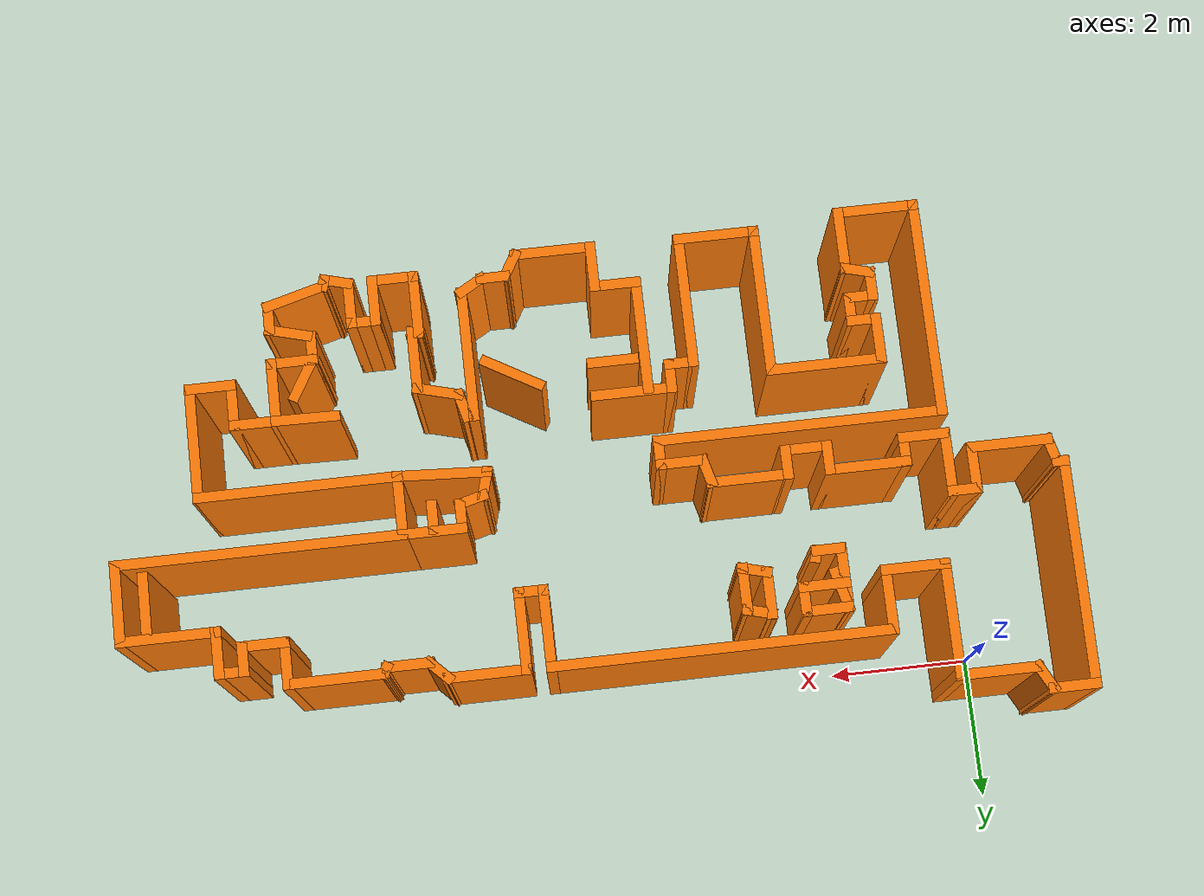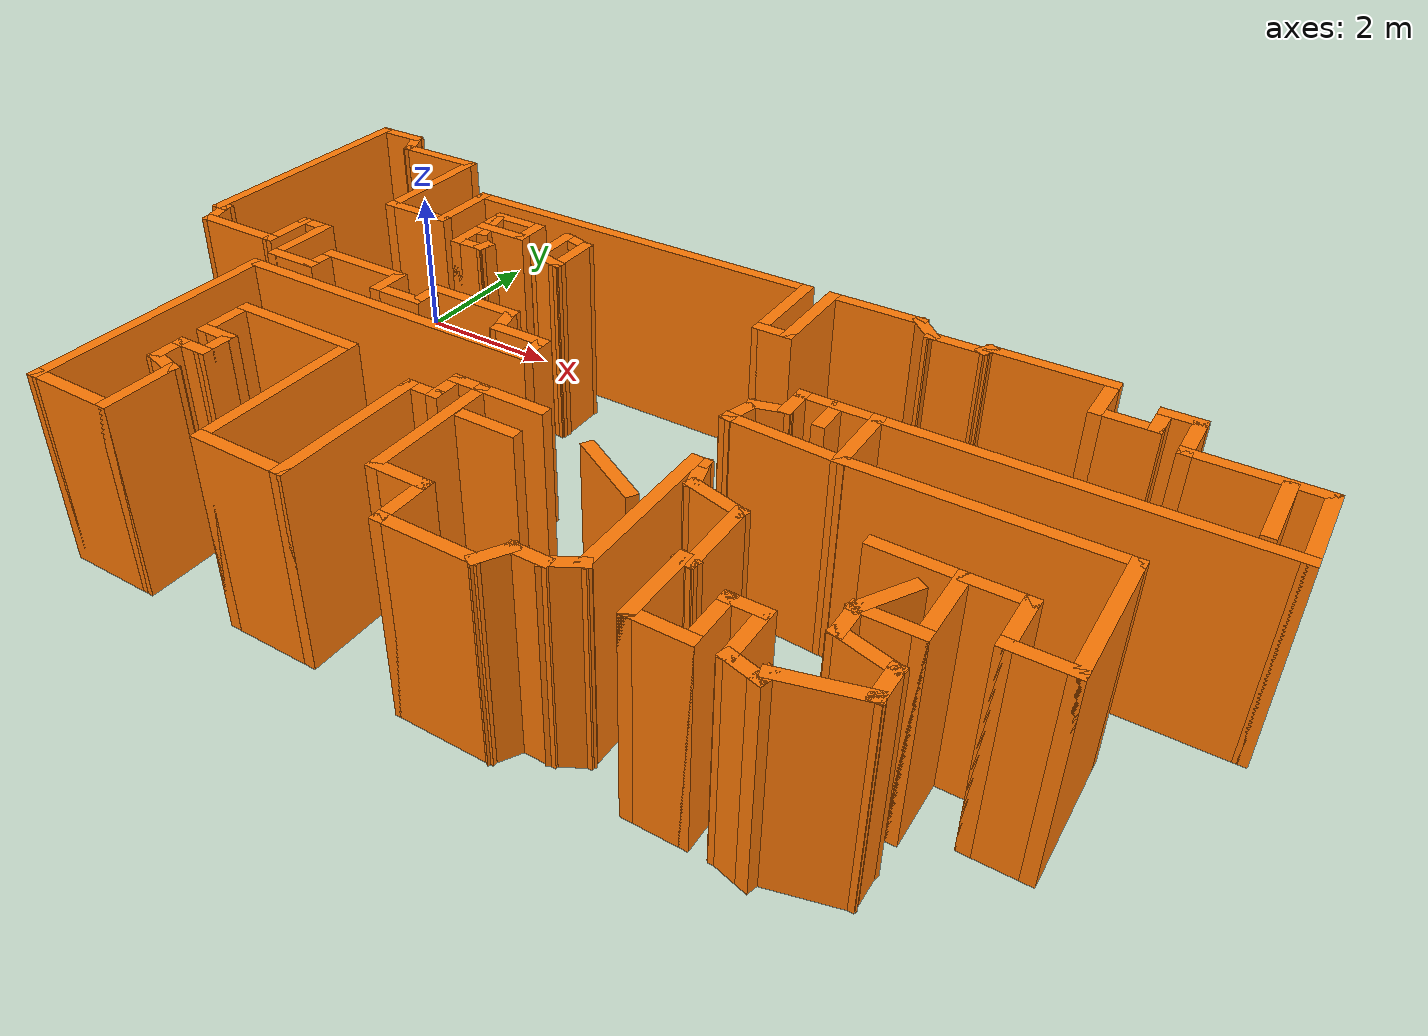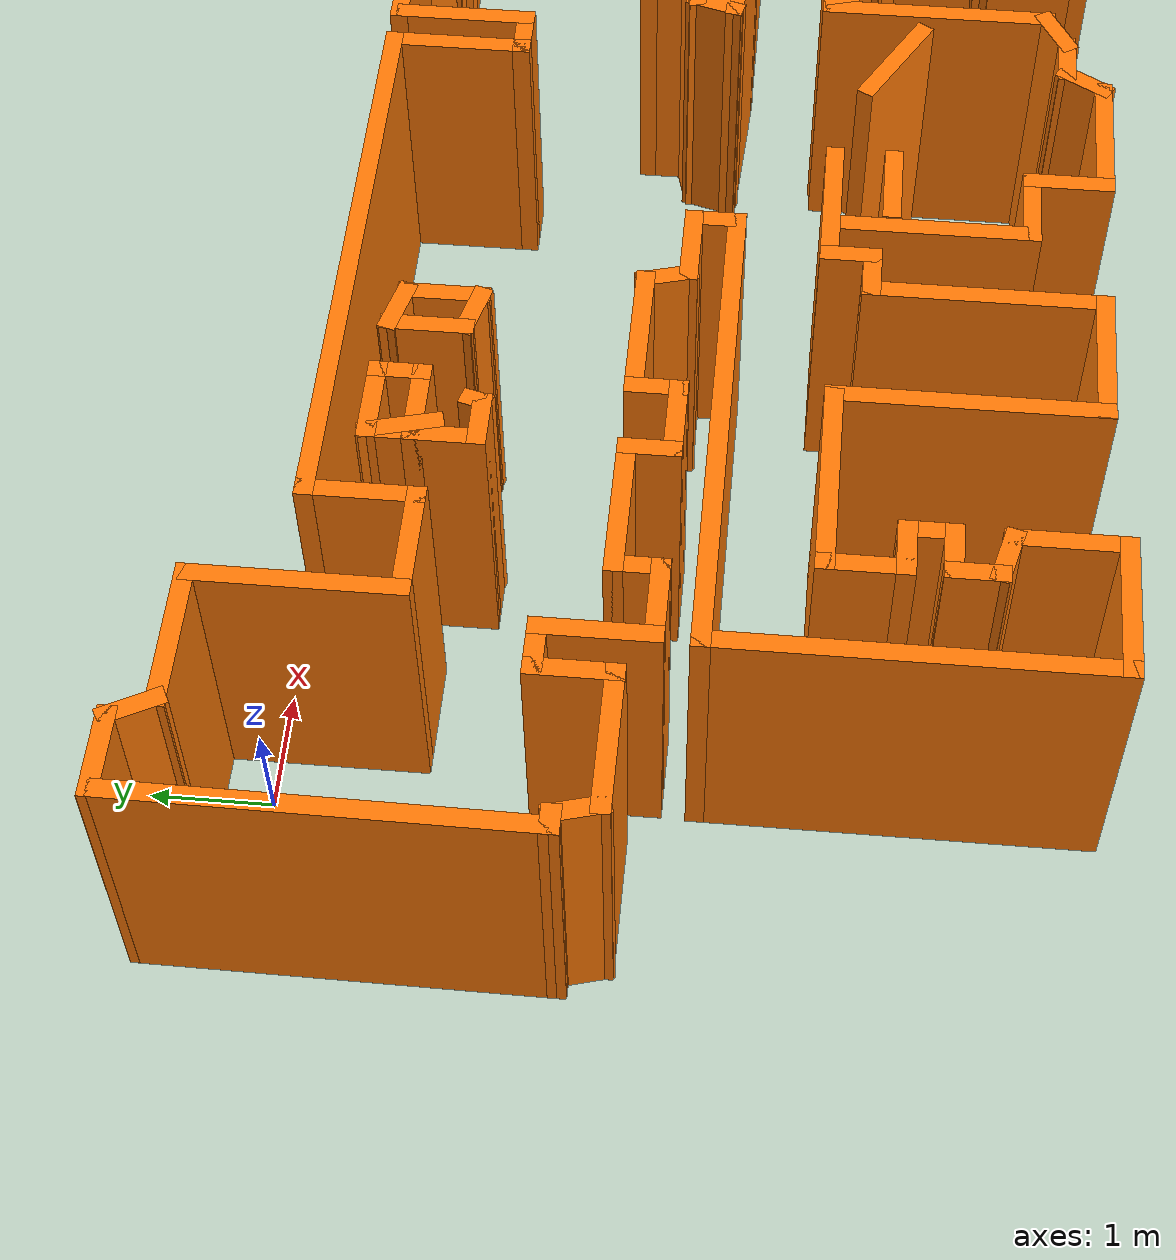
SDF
<?xml version='1.0'?>
<sdf version='1.6'>
  <model name='map_27'>
    <pose frame=''>5.37983 -2.81215 0 0 -0 0</pose>
    <link name='Wall_100'>
      <collision name='Wall_100_Collision'>
        <geometry>
          <box>
            <size>0.75 0.15 2.5</size>
          </box>
        </geometry>
        <pose frame=''>0 0 1.25 0 -0 0</pose>
      </collision>
      <visual name='Wall_100_Visual'>
        <pose frame=''>0 0 1.25 0 -0 0</pose>
        <geometry>
          <box>
            <size>0.75 0.15 2.5</size>
          </box>
        </geometry>
        <material>
          <script>
            <uri>file://media/materials/scripts/gazebo.material</uri>
            <name>Gazebo/Grey</name>
          </script>
          <ambient>0.996078 0.47451 0.0196078 1</ambient>
        </material>
        <meta>
          <layer>0</layer>
        </meta>
      </visual>
      <pose frame=''>4.04514 -2.2771 0 0 -0 0</pose>
    </link>
    <link name='Wall_101'>
      <collision name='Wall_101_Collision'>
        <geometry>
          <box>
            <size>1 0.15 2.5</size>
          </box>
        </geometry>
        <pose frame=''>0 0 1.25 0 -0 0</pose>
      </collision>
      <visual name='Wall_101_Visual'>
        <pose frame=''>0 0 1.25 0 -0 0</pose>
        <geometry>
          <box>
            <size>1 0.15 2.5</size>
          </box>
        </geometry>
        <material>
          <script>
            <uri>file://media/materials/scripts/gazebo.material</uri>
            <name>Gazebo/Grey</name>
          </script>
          <ambient>0.996078 0.47451 0.0196078 1</ambient>
        </material>
        <meta>
          <layer>0</layer>
        </meta>
      </visual>
      <pose frame=''>4.34514 -1.8521 0 0 -0 1.5708</pose>
    </link>
    <link name='Wall_102'>
      <collision name='Wall_102_Collision'>
        <geometry>
          <box>
            <size>0.75 0.15 2.5</size>
          </box>
        </geometry>
        <pose frame=''>0 0 1.25 0 -0 0</pose>
      </collision>
      <visual name='Wall_102_Visual'>
        <pose frame=''>0 0 1.25 0 -0 0</pose>
        <geometry>
          <box>
            <size>0.75 0.15 2.5</size>
          </box>
        </geometry>
        <material>
          <script>
            <uri>file://media/materials/scripts/gazebo.material</uri>
            <name>Gazebo/Grey</name>
          </script>
          <ambient>0.996078 0.47451 0.0196078 1</ambient>
        </material>
        <meta>
          <layer>0</layer>
        </meta>
      </visual>
      <pose frame=''>4.64514 -1.4271 0 0 -0 0</pose>
    </link>
    <link name='Wall_103'>
      <collision name='Wall_103_Collision'>
        <geometry>
          <box>
            <size>0.75 0.15 2.5</size>
          </box>
        </geometry>
        <pose frame=''>0 0 1.25 0 -0 0</pose>
      </collision>
      <visual name='Wall_103_Visual'>
        <pose frame=''>0 0 1.25 0 -0 0</pose>
        <geometry>
          <box>
            <size>0.75 0.15 2.5</size>
          </box>
        </geometry>
        <material>
          <script>
            <uri>file://media/materials/scripts/gazebo.material</uri>
            <name>Gazebo/Grey</name>
          </script>
          <ambient>0.996078 0.47451 0.0196078 1</ambient>
        </material>
        <meta>
          <layer>0</layer>
        </meta>
      </visual>
      <pose frame=''>4.94514 -1.7271 0 0 -0 -1.5708</pose>
    </link>
    <link name='Wall_104'>
      <collision name='Wall_104_Collision'>
        <geometry>
          <box>
            <size>0.75 0.15 2.5</size>
          </box>
        </geometry>
        <pose frame=''>0 0 1.25 0 -0 0</pose>
      </collision>
      <visual name='Wall_104_Visual'>
        <pose frame=''>0 0 1.25 0 -0 0</pose>
        <geometry>
          <box>
            <size>0.75 0.15 2.5</size>
          </box>
        </geometry>
        <material>
          <script>
            <uri>file://media/materials/scripts/gazebo.material</uri>
            <name>Gazebo/Grey</name>
          </script>
          <ambient>0.996078 0.47451 0.0196078 1</ambient>
        </material>
        <meta>
          <layer>0</layer>
        </meta>
      </visual>
      <pose frame=''>5.24514 -2.0271 0 0 -0 0</pose>
    </link>
    <link name='Wall_105'>
      <collision name='Wall_105_Collision'>
        <geometry>
          <box>
            <size>1.75 0.15 2.5</size>
          </box>
        </geometry>
        <pose frame=''>0 0 1.25 0 -0 0</pose>
      </collision>
      <visual name='Wall_105_Visual'>
        <pose frame=''>0 0 1.25 0 -0 0</pose>
        <geometry>
          <box>
            <size>1.75 0.15 2.5</size>
          </box>
        </geometry>
        <material>
          <script>
            <uri>file://media/materials/scripts/gazebo.material</uri>
            <name>Gazebo/Grey</name>
          </script>
          <ambient>0.996078 0.47451 0.0196078 1</ambient>
        </material>
        <meta>
          <layer>0</layer>
        </meta>
      </visual>
      <pose frame=''>5.54514 -1.2271 0 0 -0 1.5708</pose>
    </link>
    <link name='Wall_106'>
      <collision name='Wall_106_Collision'>
        <geometry>
          <box>
            <size>3 0.15 2.5</size>
          </box>
        </geometry>
        <pose frame=''>0 0 1.25 0 -0 0</pose>
      </collision>
      <visual name='Wall_106_Visual'>
        <pose frame=''>0 0 1.25 0 -0 0</pose>
        <geometry>
          <box>
            <size>3 0.15 2.5</size>
          </box>
        </geometry>
        <material>
          <script>
            <uri>file://media/materials/scripts/gazebo.material</uri>
            <name>Gazebo/Grey</name>
          </script>
          <ambient>0.996078 0.47451 0.0196078 1</ambient>
        </material>
        <meta>
          <layer>0</layer>
        </meta>
      </visual>
      <pose frame=''>4.12014 -0.427096 0 0 -0 3.14159</pose>
    </link>
    <link name='Wall_107'>
      <collision name='Wall_107_Collision'>
        <geometry>
          <box>
            <size>1 0.15 2.5</size>
          </box>
        </geometry>
        <pose frame=''>0 0 1.25 0 -0 0</pose>
      </collision>
      <visual name='Wall_107_Visual'>
        <pose frame=''>0 0 1.25 0 -0 0</pose>
        <geometry>
          <box>
            <size>1 0.15 2.5</size>
          </box>
        </geometry>
        <material>
          <script>
            <uri>file://media/materials/scripts/gazebo.material</uri>
            <name>Gazebo/Grey</name>
          </script>
          <ambient>0.996078 0.47451 0.0196078 1</ambient>
        </material>
        <meta>
          <layer>0</layer>
        </meta>
      </visual>
      <pose frame=''>2.69514 -0.002096 0 0 -0 1.5708</pose>
    </link>
    <link name='Wall_108'>
      <collision name='Wall_108_Collision'>
        <geometry>
          <box>
            <size>4.25 0.15 2.5</size>
          </box>
        </geometry>
        <pose frame=''>0 0 1.25 0 -0 0</pose>
      </collision>
      <visual name='Wall_108_Visual'>
        <pose frame=''>0 0 1.25 0 -0 0</pose>
        <geometry>
          <box>
            <size>4.25 0.15 2.5</size>
          </box>
        </geometry>
        <material>
          <script>
            <uri>file://media/materials/scripts/gazebo.material</uri>
            <name>Gazebo/Grey</name>
          </script>
          <ambient>0.996078 0.47451 0.0196078 1</ambient>
        </material>
        <meta>
          <layer>0</layer>
        </meta>
      </visual>
      <pose frame=''>4.74514 0.422904 0 0 -0 0</pose>
    </link>
    <link name='Wall_109'>
      <collision name='Wall_109_Collision'>
        <geometry>
          <box>
            <size>1.25 0.15 2.5</size>
          </box>
        </geometry>
        <pose frame=''>0 0 1.25 0 -0 0</pose>
      </collision>
      <visual name='Wall_109_Visual'>
        <pose frame=''>0 0 1.25 0 -0 0</pose>
        <geometry>
          <box>
            <size>1.25 0.15 2.5</size>
          </box>
        </geometry>
        <material>
          <script>
            <uri>file://media/materials/scripts/gazebo.material</uri>
            <name>Gazebo/Grey</name>
          </script>
          <ambient>0.996078 0.47451 0.0196078 1</ambient>
        </material>
        <meta>
          <layer>0</layer>
        </meta>
      </visual>
      <pose frame=''>6.79514 0.972904 0 0 -0 1.5708</pose>
    </link>
    <link name='Wall_110'>
      <collision name='Wall_110_Collision'>
        <geometry>
          <box>
            <size>1.5 0.15 2.5</size>
          </box>
        </geometry>
        <pose frame=''>0 0 1.25 0 -0 0</pose>
      </collision>
      <visual name='Wall_110_Visual'>
        <pose frame=''>0 0 1.25 0 -0 0</pose>
        <geometry>
          <box>
            <size>1.5 0.15 2.5</size>
          </box>
        </geometry>
        <material>
          <script>
            <uri>file://media/materials/scripts/gazebo.material</uri>
            <name>Gazebo/Grey</name>
          </script>
          <ambient>0.996078 0.47451 0.0196078 1</ambient>
        </material>
        <meta>
          <layer>0</layer>
        </meta>
      </visual>
      <pose frame=''>6.12014 1.5229 0 0 -0 3.14159</pose>
    </link>
    <link name='Wall_111'>
      <collision name='Wall_111_Collision'>
        <geometry>
          <box>
            <size>0.75 0.15 2.5</size>
          </box>
        </geometry>
        <pose frame=''>0 0 1.25 0 -0 0</pose>
      </collision>
      <visual name='Wall_111_Visual'>
        <pose frame=''>0 0 1.25 0 -0 0</pose>
        <geometry>
          <box>
            <size>0.75 0.15 2.5</size>
          </box>
        </geometry>
        <material>
          <script>
            <uri>file://media/materials/scripts/gazebo.material</uri>
            <name>Gazebo/Grey</name>
          </script>
          <ambient>0.996078 0.47451 0.0196078 1</ambient>
        </material>
        <meta>
          <layer>0</layer>
        </meta>
      </visual>
      <pose frame=''>5.44514 1.8229 0 0 -0 1.5708</pose>
    </link>
    <link name='Wall_112'>
      <collision name='Wall_112_Collision'>
        <geometry>
          <box>
            <size>0.5 0.15 2.5</size>
          </box>
        </geometry>
        <pose frame=''>0 0 1.25 0 -0 0</pose>
      </collision>
      <visual name='Wall_112_Visual'>
        <pose frame=''>0 0 1.25 0 -0 0</pose>
        <geometry>
          <box>
            <size>0.5 0.15 2.5</size>
          </box>
        </geometry>
        <material>
          <script>
            <uri>file://media/materials/scripts/gazebo.material</uri>
            <name>Gazebo/Grey</name>
          </script>
          <ambient>0.996078 0.47451 0.0196078 1</ambient>
        </material>
        <meta>
          <layer>0</layer>
        </meta>
      </visual>
      <pose frame=''>5.27014 2.1229 0 0 -0 3.14159</pose>
    </link>
    <link name='Wall_113'>
      <collision name='Wall_113_Collision'>
        <geometry>
          <box>
            <size>0.5 0.15 2.5</size>
          </box>
        </geometry>
        <pose frame=''>0 0 1.25 0 -0 0</pose>
      </collision>
      <visual name='Wall_113_Visual'>
        <pose frame=''>0 0 1.25 0 -0 0</pose>
        <geometry>
          <box>
            <size>0.5 0.15 2.5</size>
          </box>
        </geometry>
        <material>
          <script>
            <uri>file://media/materials/scripts/gazebo.material</uri>
            <name>Gazebo/Grey</name>
          </script>
          <ambient>0.996078 0.47451 0.0196078 1</ambient>
        </material>
        <meta>
          <layer>0</layer>
        </meta>
      </visual>
      <pose frame=''>5.09514 1.9479 0 0 -0 -1.5708</pose>
    </link>
    <link name='Wall_114'>
      <collision name='Wall_114_Collision'>
        <geometry>
          <box>
            <size>0.75 0.15 2.5</size>
          </box>
        </geometry>
        <pose frame=''>0 0 1.25 0 -0 0</pose>
      </collision>
      <visual name='Wall_114_Visual'>
        <pose frame=''>0 0 1.25 0 -0 0</pose>
        <geometry>
          <box>
            <size>0.75 0.15 2.5</size>
          </box>
        </geometry>
        <material>
          <script>
            <uri>file://media/materials/scripts/gazebo.material</uri>
            <name>Gazebo/Grey</name>
          </script>
          <ambient>0.996078 0.47451 0.0196078 1</ambient>
        </material>
        <meta>
          <layer>0</layer>
        </meta>
      </visual>
      <pose frame=''>4.79514 1.7729 0 0 -0 3.14159</pose>
    </link>
    <link name='Wall_115'>
      <collision name='Wall_115_Collision'>
        <geometry>
          <box>
            <size>0.75 0.15 2.5</size>
          </box>
        </geometry>
        <pose frame=''>0 0 1.25 0 -0 0</pose>
      </collision>
      <visual name='Wall_115_Visual'>
        <pose frame=''>0 0 1.25 0 -0 0</pose>
        <geometry>
          <box>
            <size>0.75 0.15 2.5</size>
          </box>
        </geometry>
        <material>
          <script>
            <uri>file://media/materials/scripts/gazebo.material</uri>
            <name>Gazebo/Grey</name>
          </script>
          <ambient>0.996078 0.47451 0.0196078 1</ambient>
        </material>
        <meta>
          <layer>0</layer>
        </meta>
      </visual>
      <pose frame=''>4.49514 2.0729 0 0 -0 1.5708</pose>
    </link>
    <link name='Wall_116'>
      <collision name='Wall_116_Collision'>
        <geometry>
          <box>
            <size>1.5 0.15 2.5</size>
          </box>
        </geometry>
        <pose frame=''>0 0 1.25 0 -0 0</pose>
      </collision>
      <visual name='Wall_116_Visual'>
        <pose frame=''>0 0 1.25 0 -0 0</pose>
        <geometry>
          <box>
            <size>1.5 0.15 2.5</size>
          </box>
        </geometry>
        <material>
          <script>
            <uri>file://media/materials/scripts/gazebo.material</uri>
            <name>Gazebo/Grey</name>
          </script>
          <ambient>0.996078 0.47451 0.0196078 1</ambient>
        </material>
        <meta>
          <layer>0</layer>
        </meta>
      </visual>
      <pose frame=''>3.82014 2.3729 0 0 -0 3.14159</pose>
    </link>
    <link name='Wall_117'>
      <collision name='Wall_117_Collision'>
        <geometry>
          <box>
            <size>0.25 0.15 2.5</size>
          </box>
        </geometry>
        <pose frame=''>0 0 1.25 0 -0 0</pose>
      </collision>
      <visual name='Wall_117_Visual'>
        <pose frame=''>0 0 1.25 0 -0 0</pose>
        <geometry>
          <box>
            <size>0.25 0.15 2.5</size>
          </box>
        </geometry>
        <material>
          <script>
            <uri>file://media/materials/scripts/gazebo.material</uri>
            <name>Gazebo/Grey</name>
          </script>
          <ambient>0.996078 0.47451 0.0196078 1</ambient>
        </material>
        <meta>
          <layer>0</layer>
        </meta>
      </visual>
      <pose frame=''>3.12014 2.3296 0 0 -0 -2.0944</pose>
    </link>
    <link name='Wall_118'>
      <collision name='Wall_118_Collision'>
        <geometry>
          <box>
            <size>0.75 0.15 2.5</size>
          </box>
        </geometry>
        <pose frame=''>0 0 1.25 0 -0 0</pose>
      </collision>
      <visual name='Wall_118_Visual'>
        <pose frame=''>0 0 1.25 0 -0 0</pose>
        <geometry>
          <box>
            <size>0.75 0.15 2.5</size>
          </box>
        </geometry>
        <material>
          <script>
            <uri>file://media/materials/scripts/gazebo.material</uri>
            <name>Gazebo/Grey</name>
          </script>
          <ambient>0.996078 0.47451 0.0196078 1</ambient>
        </material>
        <meta>
          <layer>0</layer>
        </meta>
      </visual>
      <pose frame=''>2.79514 2.2863 0 0 -0 3.14159</pose>
    </link>
    <link name='Wall_119'>
      <collision name='Wall_119_Collision'>
        <geometry>
          <box>
            <size>0.5 0.15 2.5</size>
          </box>
        </geometry>
        <pose frame=''>0 0 1.25 0 -0 0</pose>
      </collision>
      <visual name='Wall_119_Visual'>
        <pose frame=''>0 0 1.25 0 -0 0</pose>
        <geometry>
          <box>
            <size>0.5 0.15 2.5</size>
          </box>
        </geometry>
        <material>
          <script>
            <uri>file://media/materials/scripts/gazebo.material</uri>
            <name>Gazebo/Grey</name>
          </script>
          <ambient>0.996078 0.47451 0.0196078 1</ambient>
        </material>
        <meta>
          <layer>0</layer>
        </meta>
      </visual>
      <pose frame=''>2.3714 2.41005 0 0 -0 2.35619</pose>
    </link>
    <link name='Wall_120'>
      <collision name='Wall_120_Collision'>
        <geometry>
          <box>
            <size>1.25 0.15 2.5</size>
          </box>
        </geometry>
        <pose frame=''>0 0 1.25 0 -0 0</pose>
      </collision>
      <visual name='Wall_120_Visual'>
        <pose frame=''>0 0 1.25 0 -0 0</pose>
        <geometry>
          <box>
            <size>1.25 0.15 2.5</size>
          </box>
        </geometry>
        <material>
          <script>
            <uri>file://media/materials/scripts/gazebo.material</uri>
            <name>Gazebo/Grey</name>
          </script>
          <ambient>0.996078 0.47451 0.0196078 1</ambient>
        </material>
        <meta>
          <layer>0</layer>
        </meta>
      </visual>
      <pose frame=''>1.69765 2.53379 0 0 -0 3.14159</pose>
    </link>
    <link name='Wall_121'>
      <collision name='Wall_121_Collision'>
        <geometry>
          <box>
            <size>1.25 0.15 2.5</size>
          </box>
        </geometry>
        <pose frame=''>0 0 1.25 0 -0 0</pose>
      </collision>
      <visual name='Wall_121_Visual'>
        <pose frame=''>0 0 1.25 0 -0 0</pose>
        <geometry>
          <box>
            <size>1.25 0.15 2.5</size>
          </box>
        </geometry>
        <material>
          <script>
            <uri>file://media/materials/scripts/gazebo.material</uri>
            <name>Gazebo/Grey</name>
          </script>
          <ambient>0.996078 0.47451 0.0196078 1</ambient>
        </material>
        <meta>
          <layer>0</layer>
        </meta>
      </visual>
      <pose frame=''>1.14766 1.98379 0 0 -0 -1.5708</pose>
    </link>
    <link name='Wall_122'>
      <collision name='Wall_122_Collision'>
        <geometry>
          <box>
            <size>0.5 0.15 2.5</size>
          </box>
        </geometry>
        <pose frame=''>0 0 1.25 0 -0 0</pose>
      </collision>
      <visual name='Wall_122_Visual'>
        <pose frame=''>0 0 1.25 0 -0 0</pose>
        <geometry>
          <box>
            <size>0.5 0.15 2.5</size>
          </box>
        </geometry>
        <material>
          <script>
            <uri>file://media/materials/scripts/gazebo.material</uri>
            <name>Gazebo/Grey</name>
          </script>
          <ambient>0.996078 0.47451 0.0196078 1</ambient>
        </material>
        <meta>
          <layer>0</layer>
        </meta>
      </visual>
      <pose frame=''>0.972655 1.43379 0 0 -0 3.14159</pose>
    </link>
    <link name='Wall_123'>
      <collision name='Wall_123_Collision'>
        <geometry>
          <box>
            <size>1.25 0.15 2.5</size>
          </box>
        </geometry>
        <pose frame=''>0 0 1.25 0 -0 0</pose>
      </collision>
      <visual name='Wall_123_Visual'>
        <pose frame=''>0 0 1.25 0 -0 0</pose>
        <geometry>
          <box>
            <size>1.25 0.15 2.5</size>
          </box>
        </geometry>
        <material>
          <script>
            <uri>file://media/materials/scripts/gazebo.material</uri>
            <name>Gazebo/Grey</name>
          </script>
          <ambient>0.996078 0.47451 0.0196078 1</ambient>
        </material>
        <meta>
          <layer>0</layer>
        </meta>
      </visual>
      <pose frame=''>0.797655 1.98379 0 0 -0 1.5708</pose>
    </link>
    <link name='Wall_124'>
      <collision name='Wall_124_Collision'>
        <geometry>
          <box>
            <size>5 0.15 2.5</size>
          </box>
        </geometry>
        <pose frame=''>0 0 1.25 0 -0 0</pose>
      </collision>
      <visual name='Wall_124_Visual'>
        <pose frame=''>0 0 1.25 0 -0 0</pose>
        <geometry>
          <box>
            <size>5 0.15 2.5</size>
          </box>
        </geometry>
        <material>
          <script>
            <uri>file://media/materials/scripts/gazebo.material</uri>
            <name>Gazebo/Grey</name>
          </script>
          <ambient>0.996078 0.47451 0.0196078 1</ambient>
        </material>
        <meta>
          <layer>0</layer>
        </meta>
      </visual>
      <pose frame=''>-1.62735 2.53379 0 0 -0 3.14159</pose>
    </link>
    <link name='Wall_125'>
      <collision name='Wall_125_Collision'>
        <geometry>
          <box>
            <size>1 0.15 2.5</size>
          </box>
        </geometry>
        <pose frame=''>0 0 1.25 0 -0 0</pose>
      </collision>
      <visual name='Wall_125_Visual'>
        <pose frame=''>0 0 1.25 0 -0 0</pose>
        <geometry>
          <box>
            <size>1 0.15 2.5</size>
          </box>
        </geometry>
        <material>
          <script>
            <uri>file://media/materials/scripts/gazebo.material</uri>
            <name>Gazebo/Grey</name>
          </script>
          <ambient>0.996078 0.47451 0.0196078 1</ambient>
        </material>
        <meta>
          <layer>0</layer>
        </meta>
      </visual>
      <pose frame=''>-4.05234 2.10879 0 0 -0 -1.5708</pose>
    </link>
    <link name='Wall_126'>
      <collision name='Wall_126_Collision'>
        <geometry>
          <box>
            <size>1 0.15 2.5</size>
          </box>
        </geometry>
        <pose frame=''>0 0 1.25 0 -0 0</pose>
      </collision>
      <visual name='Wall_126_Visual'>
        <pose frame=''>0 0 1.25 0 -0 0</pose>
        <geometry>
          <box>
            <size>1 0.15 2.5</size>
          </box>
        </geometry>
        <material>
          <script>
            <uri>file://media/materials/scripts/gazebo.material</uri>
            <name>Gazebo/Grey</name>
          </script>
          <ambient>0.996078 0.47451 0.0196078 1</ambient>
        </material>
        <meta>
          <layer>0</layer>
        </meta>
      </visual>
      <pose frame=''>-4.47734 1.68379 0 0 -0 3.14159</pose>
    </link>
    <link name='Wall_127'>
      <collision name='Wall_127_Collision'>
        <geometry>
          <box>
            <size>1.75 0.15 2.5</size>
          </box>
        </geometry>
        <pose frame=''>0 0 1.25 0 -0 0</pose>
      </collision>
      <visual name='Wall_127_Visual'>
        <pose frame=''>0 0 1.25 0 -0 0</pose>
        <geometry>
          <box>
            <size>1.75 0.15 2.5</size>
          </box>
        </geometry>
        <material>
          <script>
            <uri>file://media/materials/scripts/gazebo.material</uri>
            <name>Gazebo/Grey</name>
          </script>
          <ambient>0.996078 0.47451 0.0196078 1</ambient>
        </material>
        <meta>
          <layer>0</layer>
        </meta>
      </visual>
      <pose frame=''>-4.90235 2.48379 0 0 -0 1.5708</pose>
    </link>
    <link name='Wall_128'>
      <collision name='Wall_128_Collision'>
        <geometry>
          <box>
            <size>1.25 0.15 2.5</size>
          </box>
        </geometry>
        <pose frame=''>0 0 1.25 0 -0 0</pose>
      </collision>
      <visual name='Wall_128_Visual'>
        <pose frame=''>0 0 1.25 0 -0 0</pose>
        <geometry>
          <box>
            <size>1.25 0.15 2.5</size>
          </box>
        </geometry>
        <material>
          <script>
            <uri>file://media/materials/scripts/gazebo.material</uri>
            <name>Gazebo/Grey</name>
          </script>
          <ambient>0.996078 0.47451 0.0196078 1</ambient>
        </material>
        <meta>
          <layer>0</layer>
        </meta>
      </visual>
      <pose frame=''>-5.45235 3.28379 0 0 -0 3.14159</pose>
    </link>
    <link name='Wall_132'>
      <collision name='Wall_132_Collision'>
        <geometry>
          <box>
            <size>0.75 0.15 2.5</size>
          </box>
        </geometry>
        <pose frame=''>0 0 1.25 0 -0 0</pose>
      </collision>
      <visual name='Wall_132_Visual'>
        <pose frame=''>0 0 1.25 0 -0 0</pose>
        <geometry>
          <box>
            <size>0.75 0.15 2.5</size>
          </box>
        </geometry>
        <material>
          <script>
            <uri>file://media/materials/scripts/gazebo.material</uri>
            <name>Gazebo/Grey</name>
          </script>
          <ambient>0.996078 0.47451 0.0196078 1</ambient>
        </material>
        <meta>
          <layer>0</layer>
        </meta>
      </visual>
      <pose frame=''>-6.47147 3.6078 0 0 -0 0</pose>
    </link>
    <link name='Wall_133'>
      <collision name='Wall_133_Collision'>
        <geometry>
          <box>
            <size>0.515501 0.15 2.5</size>
          </box>
        </geometry>
        <pose frame=''>0 0 1.25 0 -0 0</pose>
      </collision>
      <visual name='Wall_133_Visual'>
        <pose frame=''>0 0 1.25 0 -0 0</pose>
        <geometry>
          <box>
            <size>0.515501 0.15 2.5</size>
          </box>
        </geometry>
        <material>
          <script>
            <uri>file://media/materials/scripts/gazebo.material</uri>
            <name>Gazebo/Grey</name>
          </script>
          <ambient>0.996078 0.47451 0.0196078 1</ambient>
        </material>
        <meta>
          <layer>0</layer>
        </meta>
      </visual>
      <pose frame=''>-6.08691 3.4458 0 0 -0 -1.08972</pose>
    </link>
    <link name='Wall_135'>
      <collision name='Wall_135_Collision'>
        <geometry>
          <box>
            <size>1 0.15 2.5</size>
          </box>
        </geometry>
        <pose frame=''>0 0 1.25 0 -0 0</pose>
      </collision>
      <visual name='Wall_135_Visual'>
        <pose frame=''>0 0 1.25 0 -0 0</pose>
        <geometry>
          <box>
            <size>1 0.15 2.5</size>
          </box>
        </geometry>
        <material>
          <script>
            <uri>file://media/materials/scripts/gazebo.material</uri>
            <name>Gazebo/Grey</name>
          </script>
          <ambient>0.996078 0.47451 0.0196078 1</ambient>
        </material>
        <meta>
          <layer>0</layer>
        </meta>
      </visual>
      <pose frame=''>6.41297 1.05479 0 0 -0 -1.5708</pose>
    </link>
    <link name='Wall_138'>
      <collision name='Wall_138_Collision'>
        <geometry>
          <box>
            <size>1 0.15 2.5</size>
          </box>
        </geometry>
        <pose frame=''>0 0 1.25 0 -0 0</pose>
      </collision>
      <visual name='Wall_138_Visual'>
        <pose frame=''>0 0 1.25 0 -0 0</pose>
        <geometry>
          <box>
            <size>1 0.15 2.5</size>
          </box>
        </geometry>
        <material>
          <script>
            <uri>file://media/materials/scripts/gazebo.material</uri>
            <name>Gazebo/Grey</name>
          </script>
          <ambient>0.996078 0.47451 0.0196078 1</ambient>
        </material>
        <meta>
          <layer>0</layer>
        </meta>
      </visual>
      <pose frame=''>0.905858 -1.76282 0 0 -0 -0.523599</pose>
    </link>
    <link name='Wall_141'>
      <collision name='Wall_141_Collision'>
        <geometry>
          <box>
            <size>0.99677 0.15 2.5</size>
          </box>
        </geometry>
        <pose frame=''>0 0 1.25 0 -0 0</pose>
      </collision>
      <visual name='Wall_141_Visual'>
        <pose frame=''>0 0 1.25 0 -0 0</pose>
        <geometry>
          <box>
            <size>0.99677 0.15 2.5</size>
          </box>
        </geometry>
        <material>
          <script>
            <uri>file://media/materials/scripts/gazebo.material</uri>
            <name>Gazebo/Grey</name>
          </script>
          <ambient>0.996078 0.47451 0.0196078 1</ambient>
        </material>
        <meta>
          <layer>0</layer>
        </meta>
      </visual>
      <pose frame=''>3.92183 -1.41932 0 0 -0 -0.018375</pose>
    </link>
    <link name='Wall_143'>
      <collision name='Wall_143_Collision'>
        <geometry>
          <box>
            <size>0.75 0.15 2.5</size>
          </box>
        </geometry>
        <pose frame=''>0 0 1.25 0 -0 0</pose>
      </collision>
      <visual name='Wall_143_Visual'>
        <pose frame=''>0 0 1.25 0 -0 0</pose>
        <geometry>
          <box>
            <size>0.75 0.15 2.5</size>
          </box>
        </geometry>
        <material>
          <script>
            <uri>file://media/materials/scripts/gazebo.material</uri>
            <name>Gazebo/Grey</name>
          </script>
          <ambient>0.996078 0.47451 0.0196078 1</ambient>
        </material>
        <meta>
          <layer>0</layer>
        </meta>
      </visual>
      <pose frame=''>3.89514 -2.01729 0 0 -0 1.0472</pose>
    </link>
    <link name='Wall_148'>
      <collision name='Wall_148_Collision'>
        <geometry>
          <box>
            <size>1 0.15 2.5</size>
          </box>
        </geometry>
        <pose frame=''>0 0 1.25 0 -0 0</pose>
      </collision>
      <visual name='Wall_148_Visual'>
        <pose frame=''>0 0 1.25 0 -0 0</pose>
        <geometry>
          <box>
            <size>1 0.15 2.5</size>
          </box>
        </geometry>
        <material>
          <script>
            <uri>file://media/materials/scripts/gazebo.material</uri>
            <name>Gazebo/Grey</name>
          </script>
          <ambient>0.996078 0.47451 0.0196078 1</ambient>
        </material>
        <meta>
          <layer>0</layer>
        </meta>
      </visual>
      <pose frame=''>-3.4638 1.72558 0 0 -0 -1.5708</pose>
    </link>
    <link name='Wall_149'>
      <collision name='Wall_149_Collision'>
        <geometry>
          <box>
            <size>0.5 0.15 2.5</size>
          </box>
        </geometry>
        <pose frame=''>0 0 1.25 0 -0 0</pose>
      </collision>
      <visual name='Wall_149_Visual'>
        <pose frame=''>0 0 1.25 0 -0 0</pose>
        <geometry>
          <box>
            <size>0.5 0.15 2.5</size>
          </box>
        </geometry>
        <material>
          <script>
            <uri>file://media/materials/scripts/gazebo.material</uri>
            <name>Gazebo/Grey</name>
          </script>
          <ambient>0.996078 0.47451 0.0196078 1</ambient>
        </material>
        <meta>
          <layer>0</layer>
        </meta>
      </visual>
      <pose frame=''>-3.2888 1.30058 0 0 -0 0</pose>
    </link>
    <link name='Wall_15'>
      <collision name='Wall_15_Collision'>
        <geometry>
          <box>
            <size>3.36574 0.15 2.5</size>
          </box>
        </geometry>
        <pose frame=''>0 0 1.25 0 -0 0</pose>
      </collision>
      <visual name='Wall_15_Visual'>
        <pose frame=''>0 0 1.25 0 -0 0</pose>
        <geometry>
          <box>
            <size>3.36574 0.15 2.5</size>
          </box>
        </geometry>
        <material>
          <script>
            <uri>file://media/materials/scripts/gazebo.material</uri>
            <name>Gazebo/Grey</name>
          </script>
          <ambient>0.996078 0.47451 0.0196078 1</ambient>
        </material>
        <meta>
          <layer>0</layer>
        </meta>
      </visual>
      <pose frame=''>-6.78304 1.99998 0 0 -0 -1.57799</pose>
    </link>
    <link name='Wall_150'>
      <collision name='Wall_150_Collision'>
        <geometry>
          <box>
            <size>0.25 0.15 2.5</size>
          </box>
        </geometry>
        <pose frame=''>0 0 1.25 0 -0 0</pose>
      </collision>
      <visual name='Wall_150_Visual'>
        <pose frame=''>0 0 1.25 0 -0 0</pose>
        <geometry>
          <box>
            <size>0.25 0.15 2.5</size>
          </box>
        </geometry>
        <material>
          <script>
            <uri>file://media/materials/scripts/gazebo.material</uri>
            <name>Gazebo/Grey</name>
          </script>
          <ambient>0.996078 0.47451 0.0196078 1</ambient>
        </material>
        <meta>
          <layer>0</layer>
        </meta>
      </visual>
      <pose frame=''>-3.10086 1.34887 0 0 -0 1.309</pose>
    </link>
    <link name='Wall_152'>
      <collision name='Wall_152_Collision'>
        <geometry>
          <box>
            <size>0.671958 0.15 2.5</size>
          </box>
        </geometry>
        <pose frame=''>0 0 1.25 0 -0 0</pose>
      </collision>
      <visual name='Wall_152_Visual'>
        <pose frame=''>0 0 1.25 0 -0 0</pose>
        <geometry>
          <box>
            <size>0.671958 0.15 2.5</size>
          </box>
        </geometry>
        <material>
          <script>
            <uri>file://media/materials/scripts/gazebo.material</uri>
            <name>Gazebo/Grey</name>
          </script>
          <ambient>0.996078 0.47451 0.0196078 1</ambient>
        </material>
        <meta>
          <layer>0</layer>
        </meta>
      </visual>
      <pose frame=''>-3.3996 1.89762 0 0 -0 1.81933</pose>
    </link>
    <link name='Wall_154'>
      <collision name='Wall_154_Collision'>
        <geometry>
          <box>
            <size>0.75 0.15 2.5</size>
          </box>
        </geometry>
        <pose frame=''>0 0 1.25 0 -0 0</pose>
      </collision>
      <visual name='Wall_154_Visual'>
        <pose frame=''>0 0 1.25 0 -0 0</pose>
        <geometry>
          <box>
            <size>0.75 0.15 2.5</size>
          </box>
        </geometry>
        <material>
          <script>
            <uri>file://media/materials/scripts/gazebo.material</uri>
            <name>Gazebo/Grey</name>
          </script>
          <ambient>0.996078 0.47451 0.0196078 1</ambient>
        </material>
        <meta>
          <layer>0</layer>
        </meta>
      </visual>
      <pose frame=''>-3.1638 2.15058 0 0 -0 0</pose>
    </link>
    <link name='Wall_155'>
      <collision name='Wall_155_Collision'>
        <geometry>
          <box>
            <size>0.5 0.15 2.5</size>
          </box>
        </geometry>
        <pose frame=''>0 0 1.25 0 -0 0</pose>
      </collision>
      <visual name='Wall_155_Visual'>
        <pose frame=''>0 0 1.25 0 -0 0</pose>
        <geometry>
          <box>
            <size>0.5 0.15 2.5</size>
          </box>
        </geometry>
        <material>
          <script>
            <uri>file://media/materials/scripts/gazebo.material</uri>
            <name>Gazebo/Grey</name>
          </script>
          <ambient>0.996078 0.47451 0.0196078 1</ambient>
        </material>
        <meta>
          <layer>0</layer>
        </meta>
      </visual>
      <pose frame=''>-2.8638 1.97558 0 0 -0 -1.5708</pose>
    </link>
    <link name='Wall_156'>
      <collision name='Wall_156_Collision'>
        <geometry>
          <box>
            <size>0.75 0.15 2.5</size>
          </box>
        </geometry>
        <pose frame=''>0 0 1.25 0 -0 0</pose>
      </collision>
      <visual name='Wall_156_Visual'>
        <pose frame=''>0 0 1.25 0 -0 0</pose>
        <geometry>
          <box>
            <size>0.75 0.15 2.5</size>
          </box>
        </geometry>
        <material>
          <script>
            <uri>file://media/materials/scripts/gazebo.material</uri>
            <name>Gazebo/Grey</name>
          </script>
          <ambient>0.996078 0.47451 0.0196078 1</ambient>
        </material>
        <meta>
          <layer>0</layer>
        </meta>
      </visual>
      <pose frame=''>-3.1638 1.80058 0 0 -0 3.14159</pose>
    </link>
    <link name='Wall_158'>
      <collision name='Wall_158_Collision'>
        <geometry>
          <box>
            <size>0.75 0.15 2.5</size>
          </box>
        </geometry>
        <pose frame=''>0 0 1.25 0 -0 0</pose>
      </collision>
      <visual name='Wall_158_Visual'>
        <pose frame=''>0 0 1.25 0 -0 0</pose>
        <geometry>
          <box>
            <size>0.75 0.15 2.5</size>
          </box>
        </geometry>
        <material>
          <script>
            <uri>file://media/materials/scripts/gazebo.material</uri>
            <name>Gazebo/Grey</name>
          </script>
          <ambient>0.996078 0.47451 0.0196078 1</ambient>
        </material>
        <meta>
          <layer>0</layer>
        </meta>
      </visual>
      <pose frame=''>-2.37666 1.82745 0 0 -0 -1.5708</pose>
    </link>
    <link name='Wall_159'>
      <collision name='Wall_159_Collision'>
        <geometry>
          <box>
            <size>0.5 0.15 2.5</size>
          </box>
        </geometry>
        <pose frame=''>0 0 1.25 0 -0 0</pose>
      </collision>
      <visual name='Wall_159_Visual'>
        <pose frame=''>0 0 1.25 0 -0 0</pose>
        <geometry>
          <box>
            <size>0.5 0.15 2.5</size>
          </box>
        </geometry>
        <material>
          <script>
            <uri>file://media/materials/scripts/gazebo.material</uri>
            <name>Gazebo/Grey</name>
          </script>
          <ambient>0.996078 0.47451 0.0196078 1</ambient>
        </material>
        <meta>
          <layer>0</layer>
        </meta>
      </visual>
      <pose frame=''>-2.20762 1.48215 0 0 -0 -0.261799</pose>
    </link>
    <link name='Wall_16'>
      <collision name='Wall_16_Collision'>
        <geometry>
          <box>
            <size>0.25 0.15 2.5</size>
          </box>
        </geometry>
        <pose frame=''>0 0 1.25 0 -0 0</pose>
      </collision>
      <visual name='Wall_16_Visual'>
        <pose frame=''>0 0 1.25 0 -0 0</pose>
        <geometry>
          <box>
            <size>0.25 0.15 2.5</size>
          </box>
        </geometry>
        <material>
          <script>
            <uri>file://media/materials/scripts/gazebo.material</uri>
            <name>Gazebo/Grey</name>
          </script>
          <ambient>0.996078 0.47451 0.0196078 1</ambient>
        </material>
        <meta>
          <layer>0</layer>
        </meta>
      </visual>
      <pose frame=''>-6.7446 0.392152 0 0 -0 0</pose>
    </link>
    <link name='Wall_160'>
      <collision name='Wall_160_Collision'>
        <geometry>
          <box>
            <size>0.75 0.15 2.5</size>
          </box>
        </geometry>
        <pose frame=''>0 0 1.25 0 -0 0</pose>
      </collision>
      <visual name='Wall_160_Visual'>
        <pose frame=''>0 0 1.25 0 -0 0</pose>
        <geometry>
          <box>
            <size>0.75 0.15 2.5</size>
          </box>
        </geometry>
        <material>
          <script>
            <uri>file://media/materials/scripts/gazebo.material</uri>
            <name>Gazebo/Grey</name>
          </script>
          <ambient>0.996078 0.47451 0.0196078 1</ambient>
        </material>
        <meta>
          <layer>0</layer>
        </meta>
      </visual>
      <pose frame=''>-2.03858 1.73686 0 0 -0 1.5708</pose>
    </link>
    <link name='Wall_161'>
      <collision name='Wall_161_Collision'>
        <geometry>
          <box>
            <size>0.5 0.15 2.5</size>
          </box>
        </geometry>
        <pose frame=''>0 0 1.25 0 -0 0</pose>
      </collision>
      <visual name='Wall_161_Visual'>
        <pose frame=''>0 0 1.25 0 -0 0</pose>
        <geometry>
          <box>
            <size>0.5 0.15 2.5</size>
          </box>
        </geometry>
        <material>
          <script>
            <uri>file://media/materials/scripts/gazebo.material</uri>
            <name>Gazebo/Grey</name>
          </script>
          <ambient>0.996078 0.47451 0.0196078 1</ambient>
        </material>
        <meta>
          <layer>0</layer>
        </meta>
      </visual>
      <pose frame=''>-2.20762 2.08215 0 0 -0 2.87979</pose>
    </link>
    <link name='Wall_164'>
      <collision name='Wall_164_Collision'>
        <geometry>
          <box>
            <size>0.75 0.15 2.5</size>
          </box>
        </geometry>
        <pose frame=''>0 0 1.25 0 -0 0</pose>
      </collision>
      <visual name='Wall_164_Visual'>
        <pose frame=''>0 0 1.25 0 -0 0</pose>
        <geometry>
          <box>
            <size>0.75 0.15 2.5</size>
          </box>
        </geometry>
        <material>
          <script>
            <uri>file://media/materials/scripts/gazebo.material</uri>
            <name>Gazebo/Grey</name>
          </script>
          <ambient>0.996078 0.47451 0.0196078 1</ambient>
        </material>
        <meta>
          <layer>0</layer>
        </meta>
      </visual>
      <pose frame=''>-0.550039 -1.78163 0 0 -0 0</pose>
    </link>
    <link name='Wall_167'>
      <collision name='Wall_167_Collision'>
        <geometry>
          <box>
            <size>1 0.15 2.5</size>
          </box>
        </geometry>
        <pose frame=''>0 0 1.25 0 -0 0</pose>
      </collision>
      <visual name='Wall_167_Visual'>
        <pose frame=''>0 0 1.25 0 -0 0</pose>
        <geometry>
          <box>
            <size>1 0.15 2.5</size>
          </box>
        </geometry>
        <material>
          <script>
            <uri>file://media/materials/scripts/gazebo.material</uri>
            <name>Gazebo/Grey</name>
          </script>
          <ambient>0.996078 0.47451 0.0196078 1</ambient>
        </material>
        <meta>
          <layer>0</layer>
        </meta>
      </visual>
      <pose frame=''>2.27014 0.422904 0 0 -0 3.14159</pose>
    </link>
    <link name='Wall_168'>
      <collision name='Wall_168_Collision'>
        <geometry>
          <box>
            <size>0.5 0.15 2.5</size>
          </box>
        </geometry>
        <pose frame=''>0 0 1.25 0 -0 0</pose>
      </collision>
      <visual name='Wall_168_Visual'>
        <pose frame=''>0 0 1.25 0 -0 0</pose>
        <geometry>
          <box>
            <size>0.5 0.15 2.5</size>
          </box>
        </geometry>
        <material>
          <script>
            <uri>file://media/materials/scripts/gazebo.material</uri>
            <name>Gazebo/Grey</name>
          </script>
          <ambient>0.996078 0.47451 0.0196078 1</ambient>
        </material>
        <meta>
          <layer>0</layer>
        </meta>
      </visual>
      <pose frame=''>1.84514 0.247904 0 0 -0 -1.5708</pose>
    </link>
    <link name='Wall_169'>
      <collision name='Wall_169_Collision'>
        <geometry>
          <box>
            <size>0.5 0.15 2.5</size>
          </box>
        </geometry>
        <pose frame=''>0 0 1.25 0 -0 0</pose>
      </collision>
      <visual name='Wall_169_Visual'>
        <pose frame=''>0 0 1.25 0 -0 0</pose>
        <geometry>
          <box>
            <size>0.5 0.15 2.5</size>
          </box>
        </geometry>
        <material>
          <script>
            <uri>file://media/materials/scripts/gazebo.material</uri>
            <name>Gazebo/Grey</name>
          </script>
          <ambient>0.996078 0.47451 0.0196078 1</ambient>
        </material>
        <meta>
          <layer>0</layer>
        </meta>
      </visual>
      <pose frame=''>1.6761 0.027611 0 0 -0 -2.87979</pose>
    </link>
    <link name='Wall_17'>
      <collision name='Wall_17_Collision'>
        <geometry>
          <box>
            <size>0.5 0.15 2.5</size>
          </box>
        </geometry>
        <pose frame=''>0 0 1.25 0 -0 0</pose>
      </collision>
      <visual name='Wall_17_Visual'>
        <pose frame=''>0 0 1.25 0 -0 0</pose>
        <geometry>
          <box>
            <size>0.5 0.15 2.5</size>
          </box>
        </geometry>
        <material>
          <script>
            <uri>file://media/materials/scripts/gazebo.material</uri>
            <name>Gazebo/Grey</name>
          </script>
          <ambient>0.996078 0.47451 0.0196078 1</ambient>
        </material>
        <meta>
          <layer>0</layer>
        </meta>
      </visual>
      <pose frame=''>-6.64931 0.223115 0 0 -0 -1.309</pose>
    </link>
    <link name='Wall_170'>
      <collision name='Wall_170_Collision'>
        <geometry>
          <box>
            <size>0.5 0.15 2.5</size>
          </box>
        </geometry>
        <pose frame=''>0 0 1.25 0 -0 0</pose>
      </collision>
      <visual name='Wall_170_Visual'>
        <pose frame=''>0 0 1.25 0 -0 0</pose>
        <geometry>
          <box>
            <size>0.5 0.15 2.5</size>
          </box>
        </geometry>
        <material>
          <script>
            <uri>file://media/materials/scripts/gazebo.material</uri>
            <name>Gazebo/Grey</name>
          </script>
          <ambient>0.996078 0.47451 0.0196078 1</ambient>
        </material>
        <meta>
          <layer>0</layer>
        </meta>
      </visual>
      <pose frame=''>1.46178 -0.18672 0 0 -0 -1.8326</pose>
    </link>
    <link name='Wall_171'>
      <collision name='Wall_171_Collision'>
        <geometry>
          <box>
            <size>1.43065 0.15 2.5</size>
          </box>
        </geometry>
        <pose frame=''>0 0 1.25 0 -0 0</pose>
      </collision>
      <visual name='Wall_171_Visual'>
        <pose frame=''>0 0 1.25 0 -0 0</pose>
        <geometry>
          <box>
            <size>1.43065 0.15 2.5</size>
          </box>
        </geometry>
        <material>
          <script>
            <uri>file://media/materials/scripts/gazebo.material</uri>
            <name>Gazebo/Grey</name>
          </script>
          <ambient>0.996078 0.47451 0.0196078 1</ambient>
        </material>
        <meta>
          <layer>0</layer>
        </meta>
      </visual>
      <pose frame=''>2.05581 -0.391426 0 0 -0 -0.055734</pose>
    </link>
    <link name='Wall_175'>
      <collision name='Wall_175_Collision'>
        <geometry>
          <box>
            <size>0.5 0.15 2.5</size>
          </box>
        </geometry>
        <pose frame=''>0 0 1.25 0 -0 0</pose>
      </collision>
      <visual name='Wall_175_Visual'>
        <pose frame=''>0 0 1.25 0 -0 0</pose>
        <geometry>
          <box>
            <size>0.5 0.15 2.5</size>
          </box>
        </geometry>
        <material>
          <script>
            <uri>file://media/materials/scripts/gazebo.material</uri>
            <name>Gazebo/Grey</name>
          </script>
          <ambient>0.996078 0.47451 0.0196078 1</ambient>
        </material>
        <meta>
          <layer>0</layer>
        </meta>
      </visual>
      <pose frame=''>2.24946 0.21765 0 0 -0 -1.5708</pose>
    </link>
    <link name='Wall_18'>
      <collision name='Wall_18_Collision'>
        <geometry>
          <box>
            <size>1.25 0.15 2.5</size>
          </box>
        </geometry>
        <pose frame=''>0 0 1.25 0 -0 0</pose>
      </collision>
      <visual name='Wall_18_Visual'>
        <pose frame=''>0 0 1.25 0 -0 0</pose>
        <geometry>
          <box>
            <size>1.25 0.15 2.5</size>
          </box>
        </geometry>
        <material>
          <script>
            <uri>file://media/materials/scripts/gazebo.material</uri>
            <name>Gazebo/Grey</name>
          </script>
          <ambient>0.996078 0.47451 0.0196078 1</ambient>
        </material>
        <meta>
          <layer>0</layer>
        </meta>
      </visual>
      <pose frame=''>-6.05402 0.054078 0 0 -0 0</pose>
    </link>
    <link name='Wall_19'>
      <collision name='Wall_19_Collision'>
        <geometry>
          <box>
            <size>0.75 0.15 2.5</size>
          </box>
        </geometry>
        <pose frame=''>0 0 1.25 0 -0 0</pose>
      </collision>
      <visual name='Wall_19_Visual'>
        <pose frame=''>0 0 1.25 0 -0 0</pose>
        <geometry>
          <box>
            <size>0.75 0.15 2.5</size>
          </box>
        </geometry>
        <material>
          <script>
            <uri>file://media/materials/scripts/gazebo.material</uri>
            <name>Gazebo/Grey</name>
          </script>
          <ambient>0.996078 0.47451 0.0196078 1</ambient>
        </material>
        <meta>
          <layer>0</layer>
        </meta>
      </visual>
      <pose frame=''>-5.50402 0.354078 0 0 -0 1.5708</pose>
    </link>
    <link name='Wall_20'>
      <collision name='Wall_20_Collision'>
        <geometry>
          <box>
            <size>0.5 0.15 2.5</size>
          </box>
        </geometry>
        <pose frame=''>0 0 1.25 0 -0 0</pose>
      </collision>
      <visual name='Wall_20_Visual'>
        <pose frame=''>0 0 1.25 0 -0 0</pose>
        <geometry>
          <box>
            <size>0.5 0.15 2.5</size>
          </box>
        </geometry>
        <material>
          <script>
            <uri>file://media/materials/scripts/gazebo.material</uri>
            <name>Gazebo/Grey</name>
          </script>
          <ambient>0.996078 0.47451 0.0196078 1</ambient>
        </material>
        <meta>
          <layer>0</layer>
        </meta>
      </visual>
      <pose frame=''>-5.32902 0.654078 0 0 -0 0</pose>
    </link>
    <link name='Wall_21'>
      <collision name='Wall_21_Collision'>
        <geometry>
          <box>
            <size>1 0.15 2.5</size>
          </box>
        </geometry>
        <pose frame=''>0 0 1.25 0 -0 0</pose>
      </collision>
      <visual name='Wall_21_Visual'>
        <pose frame=''>0 0 1.25 0 -0 0</pose>
        <geometry>
          <box>
            <size>1 0.15 2.5</size>
          </box>
        </geometry>
        <material>
          <script>
            <uri>file://media/materials/scripts/gazebo.material</uri>
            <name>Gazebo/Grey</name>
          </script>
          <ambient>0.996078 0.47451 0.0196078 1</ambient>
        </material>
        <meta>
          <layer>0</layer>
        </meta>
      </visual>
      <pose frame=''>-5.15402 0.229078 0 0 -0 -1.5708</pose>
    </link>
    <link name='Wall_22'>
      <collision name='Wall_22_Collision'>
        <geometry>
          <box>
            <size>0.75 0.15 2.5</size>
          </box>
        </geometry>
        <pose frame=''>0 0 1.25 0 -0 0</pose>
      </collision>
      <visual name='Wall_22_Visual'>
        <pose frame=''>0 0 1.25 0 -0 0</pose>
        <geometry>
          <box>
            <size>0.75 0.15 2.5</size>
          </box>
        </geometry>
        <material>
          <script>
            <uri>file://media/materials/scripts/gazebo.material</uri>
            <name>Gazebo/Grey</name>
          </script>
          <ambient>0.996078 0.47451 0.0196078 1</ambient>
        </material>
        <meta>
          <layer>0</layer>
        </meta>
      </visual>
      <pose frame=''>-4.85402 -0.195922 0 0 -0 0</pose>
    </link>
    <link name='Wall_23'>
      <collision name='Wall_23_Collision'>
        <geometry>
          <box>
            <size>0.5 0.15 2.5</size>
          </box>
        </geometry>
        <pose frame=''>0 0 1.25 0 -0 0</pose>
      </collision>
      <visual name='Wall_23_Visual'>
        <pose frame=''>0 0 1.25 0 -0 0</pose>
        <geometry>
          <box>
            <size>0.5 0.15 2.5</size>
          </box>
        </geometry>
        <material>
          <script>
            <uri>file://media/materials/scripts/gazebo.material</uri>
            <name>Gazebo/Grey</name>
          </script>
          <ambient>0.996078 0.47451 0.0196078 1</ambient>
        </material>
        <meta>
          <layer>0</layer>
        </meta>
      </visual>
      <pose frame=''>-4.55402 -0.020922 0 0 -0 1.5708</pose>
    </link>
    <link name='Wall_24'>
      <collision name='Wall_24_Collision'>
        <geometry>
          <box>
            <size>1.25 0.15 2.5</size>
          </box>
        </geometry>
        <pose frame=''>0 0 1.25 0 -0 0</pose>
      </collision>
      <visual name='Wall_24_Visual'>
        <pose frame=''>0 0 1.25 0 -0 0</pose>
        <geometry>
          <box>
            <size>1.25 0.15 2.5</size>
          </box>
        </geometry>
        <material>
          <script>
            <uri>file://media/materials/scripts/gazebo.material</uri>
            <name>Gazebo/Grey</name>
          </script>
          <ambient>0.996078 0.47451 0.0196078 1</ambient>
        </material>
        <meta>
          <layer>0</layer>
        </meta>
      </visual>
      <pose frame=''>-4.00402 0.154078 0 0 -0 0</pose>
    </link>
    <link name='Wall_25'>
      <collision name='Wall_25_Collision'>
        <geometry>
          <box>
            <size>0.5 0.15 2.5</size>
          </box>
        </geometry>
        <pose frame=''>0 0 1.25 0 -0 0</pose>
      </collision>
      <visual name='Wall_25_Visual'>
        <pose frame=''>0 0 1.25 0 -0 0</pose>
        <geometry>
          <box>
            <size>0.5 0.15 2.5</size>
          </box>
        </geometry>
        <material>
          <script>
            <uri>file://media/materials/scripts/gazebo.material</uri>
            <name>Gazebo/Grey</name>
          </script>
          <ambient>0.996078 0.47451 0.0196078 1</ambient>
        </material>
        <meta>
          <layer>0</layer>
        </meta>
      </visual>
      <pose frame=''>-3.45402 -0.020922 0 0 -0 -1.5708</pose>
    </link>
    <link name='Wall_26'>
      <collision name='Wall_26_Collision'>
        <geometry>
          <box>
            <size>0.75 0.15 2.5</size>
          </box>
        </geometry>
        <pose frame=''>0 0 1.25 0 -0 0</pose>
      </collision>
      <visual name='Wall_26_Visual'>
        <pose frame=''>0 0 1.25 0 -0 0</pose>
        <geometry>
          <box>
            <size>0.75 0.15 2.5</size>
          </box>
        </geometry>
        <material>
          <script>
            <uri>file://media/materials/scripts/gazebo.material</uri>
            <name>Gazebo/Grey</name>
          </script>
          <ambient>0.996078 0.47451 0.0196078 1</ambient>
        </material>
        <meta>
          <layer>0</layer>
        </meta>
      </visual>
      <pose frame=''>-3.15402 -0.195922 0 0 -0 0</pose>
    </link>
    <link name='Wall_27'>
      <collision name='Wall_27_Collision'>
        <geometry>
          <box>
            <size>0.5 0.15 2.5</size>
          </box>
        </geometry>
        <pose frame=''>0 0 1.25 0 -0 0</pose>
      </collision>
      <visual name='Wall_27_Visual'>
        <pose frame=''>0 0 1.25 0 -0 0</pose>
        <geometry>
          <box>
            <size>0.5 0.15 2.5</size>
          </box>
        </geometry>
        <material>
          <script>
            <uri>file://media/materials/scripts/gazebo.material</uri>
            <name>Gazebo/Grey</name>
          </script>
          <ambient>0.996078 0.47451 0.0196078 1</ambient>
        </material>
        <meta>
          <layer>0</layer>
        </meta>
      </visual>
      <pose frame=''>-2.85402 -0.020922 0 0 -0 1.5708</pose>
    </link>
    <link name='Wall_28'>
      <collision name='Wall_28_Collision'>
        <geometry>
          <box>
            <size>1.25 0.15 2.5</size>
          </box>
        </geometry>
        <pose frame=''>0 0 1.25 0 -0 0</pose>
      </collision>
      <visual name='Wall_28_Visual'>
        <pose frame=''>0 0 1.25 0 -0 0</pose>
        <geometry>
          <box>
            <size>1.25 0.15 2.5</size>
          </box>
        </geometry>
        <material>
          <script>
            <uri>file://media/materials/scripts/gazebo.material</uri>
            <name>Gazebo/Grey</name>
          </script>
          <ambient>0.996078 0.47451 0.0196078 1</ambient>
        </material>
        <meta>
          <layer>0</layer>
        </meta>
      </visual>
      <pose frame=''>-2.30402 0.154078 0 0 -0 0</pose>
    </link>
    <link name='Wall_29'>
      <collision name='Wall_29_Collision'>
        <geometry>
          <box>
            <size>0.5 0.15 2.5</size>
          </box>
        </geometry>
        <pose frame=''>0 0 1.25 0 -0 0</pose>
      </collision>
      <visual name='Wall_29_Visual'>
        <pose frame=''>0 0 1.25 0 -0 0</pose>
        <geometry>
          <box>
            <size>0.5 0.15 2.5</size>
          </box>
        </geometry>
        <material>
          <script>
            <uri>file://media/materials/scripts/gazebo.material</uri>
            <name>Gazebo/Grey</name>
          </script>
          <ambient>0.996078 0.47451 0.0196078 1</ambient>
        </material>
        <meta>
          <layer>0</layer>
        </meta>
      </visual>
      <pose frame=''>-1.70873 -0.014959 0 0 -0 -1.309</pose>
    </link>
    <link name='Wall_30'>
      <collision name='Wall_30_Collision'>
        <geometry>
          <box>
            <size>0.75 0.15 2.5</size>
          </box>
        </geometry>
        <pose frame=''>0 0 1.25 0 -0 0</pose>
      </collision>
      <visual name='Wall_30_Visual'>
        <pose frame=''>0 0 1.25 0 -0 0</pose>
        <geometry>
          <box>
            <size>0.75 0.15 2.5</size>
          </box>
        </geometry>
        <material>
          <script>
            <uri>file://media/materials/scripts/gazebo.material</uri>
            <name>Gazebo/Grey</name>
          </script>
          <ambient>0.996078 0.47451 0.0196078 1</ambient>
        </material>
        <meta>
          <layer>0</layer>
        </meta>
      </visual>
      <pose frame=''>-1.36343 -0.183996 0 0 -0 0</pose>
    </link>
    <link name='Wall_31'>
      <collision name='Wall_31_Collision'>
        <geometry>
          <box>
            <size>0.5 0.15 2.5</size>
          </box>
        </geometry>
        <pose frame=''>0 0 1.25 0 -0 0</pose>
      </collision>
      <visual name='Wall_31_Visual'>
        <pose frame=''>0 0 1.25 0 -0 0</pose>
        <geometry>
          <box>
            <size>0.5 0.15 2.5</size>
          </box>
        </geometry>
        <material>
          <script>
            <uri>file://media/materials/scripts/gazebo.material</uri>
            <name>Gazebo/Grey</name>
          </script>
          <ambient>0.996078 0.47451 0.0196078 1</ambient>
        </material>
        <meta>
          <layer>0</layer>
        </meta>
      </visual>
      <pose frame=''>-1.06343 -0.358996 0 0 -0 -1.5708</pose>
    </link>
    <link name='Wall_32'>
      <collision name='Wall_32_Collision'>
        <geometry>
          <box>
            <size>4.25 0.15 2.5</size>
          </box>
        </geometry>
        <pose frame=''>0 0 1.25 0 -0 0</pose>
      </collision>
      <visual name='Wall_32_Visual'>
        <pose frame=''>0 0 1.25 0 -0 0</pose>
        <geometry>
          <box>
            <size>4.25 0.15 2.5</size>
          </box>
        </geometry>
        <material>
          <script>
            <uri>file://media/materials/scripts/gazebo.material</uri>
            <name>Gazebo/Grey</name>
          </script>
          <ambient>0.996078 0.47451 0.0196078 1</ambient>
        </material>
        <meta>
          <layer>0</layer>
        </meta>
      </visual>
      <pose frame=''>-3.11343 -0.533996 0 0 -0 3.14159</pose>
    </link>
    <link name='Wall_33'>
      <collision name='Wall_33_Collision'>
        <geometry>
          <box>
            <size>3.25 0.15 2.5</size>
          </box>
        </geometry>
        <pose frame=''>0 0 1.25 0 -0 0</pose>
      </collision>
      <visual name='Wall_33_Visual'>
        <pose frame=''>0 0 1.25 0 -0 0</pose>
        <geometry>
          <box>
            <size>3.25 0.15 2.5</size>
          </box>
        </geometry>
        <material>
          <script>
            <uri>file://media/materials/scripts/gazebo.material</uri>
            <name>Gazebo/Grey</name>
          </script>
          <ambient>0.996078 0.47451 0.0196078 1</ambient>
        </material>
        <meta>
          <layer>0</layer>
        </meta>
      </visual>
      <pose frame=''>-5.16343 -2.084 0 0 -0 -1.5708</pose>
    </link>
    <link name='Wall_34'>
      <collision name='Wall_34_Collision'>
        <geometry>
          <box>
            <size>1.25 0.15 2.5</size>
          </box>
        </geometry>
        <pose frame=''>0 0 1.25 0 -0 0</pose>
      </collision>
      <visual name='Wall_34_Visual'>
        <pose frame=''>0 0 1.25 0 -0 0</pose>
        <geometry>
          <box>
            <size>1.25 0.15 2.5</size>
          </box>
        </geometry>
        <material>
          <script>
            <uri>file://media/materials/scripts/gazebo.material</uri>
            <name>Gazebo/Grey</name>
          </script>
          <ambient>0.996078 0.47451 0.0196078 1</ambient>
        </material>
        <meta>
          <layer>0</layer>
        </meta>
      </visual>
      <pose frame=''>-4.61343 -3.634 0 0 -0 0</pose>
    </link>
    <link name='Wall_35'>
      <collision name='Wall_35_Collision'>
        <geometry>
          <box>
            <size>1 0.15 2.5</size>
          </box>
        </geometry>
        <pose frame=''>0 0 1.25 0 -0 0</pose>
      </collision>
      <visual name='Wall_35_Visual'>
        <pose frame=''>0 0 1.25 0 -0 0</pose>
        <geometry>
          <box>
            <size>1 0.15 2.5</size>
          </box>
        </geometry>
        <material>
          <script>
            <uri>file://media/materials/scripts/gazebo.material</uri>
            <name>Gazebo/Grey</name>
          </script>
          <ambient>0.996078 0.47451 0.0196078 1</ambient>
        </material>
        <meta>
          <layer>0</layer>
        </meta>
      </visual>
      <pose frame=''>-4.06343 -3.209 0 0 -0 1.5708</pose>
    </link>
    <link name='Wall_36'>
      <collision name='Wall_36_Collision'>
        <geometry>
          <box>
            <size>0.5 0.15 2.5</size>
          </box>
        </geometry>
        <pose frame=''>0 0 1.25 0 -0 0</pose>
      </collision>
      <visual name='Wall_36_Visual'>
        <pose frame=''>0 0 1.25 0 -0 0</pose>
        <geometry>
          <box>
            <size>0.5 0.15 2.5</size>
          </box>
        </geometry>
        <material>
          <script>
            <uri>file://media/materials/scripts/gazebo.material</uri>
            <name>Gazebo/Grey</name>
          </script>
          <ambient>0.996078 0.47451 0.0196078 1</ambient>
        </material>
        <meta>
          <layer>0</layer>
        </meta>
      </visual>
      <pose frame=''>-4.23247 -2.7387 0 0 -0 2.87979</pose>
    </link>
    <link name='Wall_37'>
      <collision name='Wall_37_Collision'>
        <geometry>
          <box>
            <size>0.5 0.15 2.5</size>
          </box>
        </geometry>
        <pose frame=''>0 0 1.25 0 -0 0</pose>
      </collision>
      <visual name='Wall_37_Visual'>
        <pose frame=''>0 0 1.25 0 -0 0</pose>
        <geometry>
          <box>
            <size>0.5 0.15 2.5</size>
          </box>
        </geometry>
        <material>
          <script>
            <uri>file://media/materials/scripts/gazebo.material</uri>
            <name>Gazebo/Grey</name>
          </script>
          <ambient>0.996078 0.47451 0.0196078 1</ambient>
        </material>
        <meta>
          <layer>0</layer>
        </meta>
      </visual>
      <pose frame=''>-4.40151 -2.51841 0 0 -0 1.5708</pose>
    </link>
    <link name='Wall_41'>
      <collision name='Wall_41_Collision'>
        <geometry>
          <box>
            <size>0.5 0.15 2.5</size>
          </box>
        </geometry>
        <pose frame=''>0 0 1.25 0 -0 0</pose>
      </collision>
      <visual name='Wall_41_Visual'>
        <pose frame=''>0 0 1.25 0 -0 0</pose>
        <geometry>
          <box>
            <size>0.5 0.15 2.5</size>
          </box>
        </geometry>
        <material>
          <script>
            <uri>file://media/materials/scripts/gazebo.material</uri>
            <name>Gazebo/Grey</name>
          </script>
          <ambient>0.996078 0.47451 0.0196078 1</ambient>
        </material>
        <meta>
          <layer>0</layer>
        </meta>
      </visual>
      <pose frame=''>-4.22651 -2.34341 0 0 -0 0</pose>
    </link>
    <link name='Wall_42'>
      <collision name='Wall_42_Collision'>
        <geometry>
          <box>
            <size>0.5 0.15 2.5</size>
          </box>
        </geometry>
        <pose frame=''>0 0 1.25 0 -0 0</pose>
      </collision>
      <visual name='Wall_42_Visual'>
        <pose frame=''>0 0 1.25 0 -0 0</pose>
        <geometry>
          <box>
            <size>0.5 0.15 2.5</size>
          </box>
        </geometry>
        <material>
          <script>
            <uri>file://media/materials/scripts/gazebo.material</uri>
            <name>Gazebo/Grey</name>
          </script>
          <ambient>0.996078 0.47451 0.0196078 1</ambient>
        </material>
        <meta>
          <layer>0</layer>
        </meta>
      </visual>
      <pose frame=''>-4.05151 -2.16841 0 0 -0 1.5708</pose>
    </link>
    <link name='Wall_43'>
      <collision name='Wall_43_Collision'>
        <geometry>
          <box>
            <size>0.5 0.15 2.5</size>
          </box>
        </geometry>
        <pose frame=''>0 0 1.25 0 -0 0</pose>
      </collision>
      <visual name='Wall_43_Visual'>
        <pose frame=''>0 0 1.25 0 -0 0</pose>
        <geometry>
          <box>
            <size>0.5 0.15 2.5</size>
          </box>
        </geometry>
        <material>
          <script>
            <uri>file://media/materials/scripts/gazebo.material</uri>
            <name>Gazebo/Grey</name>
          </script>
          <ambient>0.996078 0.47451 0.0196078 1</ambient>
        </material>
        <meta>
          <layer>0</layer>
        </meta>
      </visual>
      <pose frame=''>-4.22651 -1.99341 0 0 -0 3.14159</pose>
    </link>
    <link name='Wall_46'>
      <collision name='Wall_46_Collision'>
        <geometry>
          <box>
            <size>0.75 0.15 2.5</size>
          </box>
        </geometry>
        <pose frame=''>0 0 1.25 0 -0 0</pose>
      </collision>
      <visual name='Wall_46_Visual'>
        <pose frame=''>0 0 1.25 0 -0 0</pose>
        <geometry>
          <box>
            <size>0.75 0.15 2.5</size>
          </box>
        </geometry>
        <material>
          <script>
            <uri>file://media/materials/scripts/gazebo.material</uri>
            <name>Gazebo/Grey</name>
          </script>
          <ambient>0.996078 0.47451 0.0196078 1</ambient>
        </material>
        <meta>
          <layer>0</layer>
        </meta>
      </visual>
      <pose frame=''>-4.40151 -1.69341 0 0 -0 1.5708</pose>
    </link>
    <link name='Wall_47'>
      <collision name='Wall_47_Collision'>
        <geometry>
          <box>
            <size>1.75 0.15 2.5</size>
          </box>
        </geometry>
        <pose frame=''>0 0 1.25 0 -0 0</pose>
      </collision>
      <visual name='Wall_47_Visual'>
        <pose frame=''>0 0 1.25 0 -0 0</pose>
        <geometry>
          <box>
            <size>1.75 0.15 2.5</size>
          </box>
        </geometry>
        <material>
          <script>
            <uri>file://media/materials/scripts/gazebo.material</uri>
            <name>Gazebo/Grey</name>
          </script>
          <ambient>0.996078 0.47451 0.0196078 1</ambient>
        </material>
        <meta>
          <layer>0</layer>
        </meta>
      </visual>
      <pose frame=''>-3.60151 -1.39341 0 0 -0 0</pose>
    </link>
    <link name='Wall_48'>
      <collision name='Wall_48_Collision'>
        <geometry>
          <box>
            <size>2.25 0.15 2.5</size>
          </box>
        </geometry>
        <pose frame=''>0 0 1.25 0 -0 0</pose>
      </collision>
      <visual name='Wall_48_Visual'>
        <pose frame=''>0 0 1.25 0 -0 0</pose>
        <geometry>
          <box>
            <size>2.25 0.15 2.5</size>
          </box>
        </geometry>
        <material>
          <script>
            <uri>file://media/materials/scripts/gazebo.material</uri>
            <name>Gazebo/Grey</name>
          </script>
          <ambient>0.996078 0.47451 0.0196078 1</ambient>
        </material>
        <meta>
          <layer>0</layer>
        </meta>
      </visual>
      <pose frame=''>-2.80151 -2.44341 0 0 -0 -1.5708</pose>
    </link>
    <link name='Wall_51'>
      <collision name='Wall_51_Collision'>
        <geometry>
          <box>
            <size>1.25 0.15 2.5</size>
          </box>
        </geometry>
        <pose frame=''>0 0 1.25 0 -0 0</pose>
      </collision>
      <visual name='Wall_51_Visual'>
        <pose frame=''>0 0 1.25 0 -0 0</pose>
        <geometry>
          <box>
            <size>1.25 0.15 2.5</size>
          </box>
        </geometry>
        <material>
          <script>
            <uri>file://media/materials/scripts/gazebo.material</uri>
            <name>Gazebo/Grey</name>
          </script>
          <ambient>0.996078 0.47451 0.0196078 1</ambient>
        </material>
        <meta>
          <layer>0</layer>
        </meta>
      </visual>
      <pose frame=''>-2.25151 -3.49341 0 0 -0 0</pose>
    </link>
    <link name='Wall_54'>
      <collision name='Wall_54_Collision'>
        <geometry>
          <box>
            <size>2 0.15 2.5</size>
          </box>
        </geometry>
        <pose frame=''>0 0 1.25 0 -0 0</pose>
      </collision>
      <visual name='Wall_54_Visual'>
        <pose frame=''>0 0 1.25 0 -0 0</pose>
        <geometry>
          <box>
            <size>2 0.15 2.5</size>
          </box>
        </geometry>
        <material>
          <script>
            <uri>file://media/materials/scripts/gazebo.material</uri>
            <name>Gazebo/Grey</name>
          </script>
          <ambient>0.996078 0.47451 0.0196078 1</ambient>
        </material>
        <meta>
          <layer>0</layer>
        </meta>
      </visual>
      <pose frame=''>-1.70151 -2.56841 0 0 -0 1.5708</pose>
    </link>
    <link name='Wall_70'>
      <collision name='Wall_70_Collision'>
        <geometry>
          <box>
            <size>0.5 0.15 2.5</size>
          </box>
        </geometry>
        <pose frame=''>0 0 1.25 0 -0 0</pose>
      </collision>
      <visual name='Wall_70_Visual'>
        <pose frame=''>0 0 1.25 0 -0 0</pose>
        <geometry>
          <box>
            <size>0.5 0.15 2.5</size>
          </box>
        </geometry>
        <material>
          <script>
            <uri>file://media/materials/scripts/gazebo.material</uri>
            <name>Gazebo/Grey</name>
          </script>
          <ambient>0.996078 0.47451 0.0196078 1</ambient>
        </material>
        <meta>
          <layer>0</layer>
        </meta>
      </visual>
      <pose frame=''>-1.52651 -1.64341 0 0 -0 0</pose>
    </link>
    <link name='Wall_71'>
      <collision name='Wall_71_Collision'>
        <geometry>
          <box>
            <size>0.5 0.15 2.5</size>
          </box>
        </geometry>
        <pose frame=''>0 0 1.25 0 -0 0</pose>
      </collision>
      <visual name='Wall_71_Visual'>
        <pose frame=''>0 0 1.25 0 -0 0</pose>
        <geometry>
          <box>
            <size>0.5 0.15 2.5</size>
          </box>
        </geometry>
        <material>
          <script>
            <uri>file://media/materials/scripts/gazebo.material</uri>
            <name>Gazebo/Grey</name>
          </script>
          <ambient>0.996078 0.47451 0.0196078 1</ambient>
        </material>
        <meta>
          <layer>0</layer>
        </meta>
      </visual>
      <pose frame=''>-1.35151 -1.46841 0 0 -0 1.5708</pose>
    </link>
    <link name='Wall_72'>
      <collision name='Wall_72_Collision'>
        <geometry>
          <box>
            <size>1.25 0.15 2.5</size>
          </box>
        </geometry>
        <pose frame=''>0 0 1.25 0 -0 0</pose>
      </collision>
      <visual name='Wall_72_Visual'>
        <pose frame=''>0 0 1.25 0 -0 0</pose>
        <geometry>
          <box>
            <size>1.25 0.15 2.5</size>
          </box>
        </geometry>
        <material>
          <script>
            <uri>file://media/materials/scripts/gazebo.material</uri>
            <name>Gazebo/Grey</name>
          </script>
          <ambient>0.996078 0.47451 0.0196078 1</ambient>
        </material>
        <meta>
          <layer>0</layer>
        </meta>
      </visual>
      <pose frame=''>-0.801506 -1.29341 0 0 -0 0</pose>
    </link>
    <link name='Wall_74'>
      <collision name='Wall_74_Collision'>
        <geometry>
          <box>
            <size>1.75 0.15 2.5</size>
          </box>
        </geometry>
        <pose frame=''>0 0 1.25 0 -0 0</pose>
      </collision>
      <visual name='Wall_74_Visual'>
        <pose frame=''>0 0 1.25 0 -0 0</pose>
        <geometry>
          <box>
            <size>1.75 0.15 2.5</size>
          </box>
        </geometry>
        <material>
          <script>
            <uri>file://media/materials/scripts/gazebo.material</uri>
            <name>Gazebo/Grey</name>
          </script>
          <ambient>0.996078 0.47451 0.0196078 1</ambient>
        </material>
        <meta>
          <layer>0</layer>
        </meta>
      </visual>
      <pose frame=''>-1.01195 -2.11902 0 0 -0 -1.5708</pose>
    </link>
    <link name='Wall_75'>
      <collision name='Wall_75_Collision'>
        <geometry>
          <box>
            <size>0.75 0.15 2.5</size>
          </box>
        </geometry>
        <pose frame=''>0 0 1.25 0 -0 0</pose>
      </collision>
      <visual name='Wall_75_Visual'>
        <pose frame=''>0 0 1.25 0 -0 0</pose>
        <geometry>
          <box>
            <size>0.75 0.15 2.5</size>
          </box>
        </geometry>
        <material>
          <script>
            <uri>file://media/materials/scripts/gazebo.material</uri>
            <name>Gazebo/Grey</name>
          </script>
          <ambient>0.996078 0.47451 0.0196078 1</ambient>
        </material>
        <meta>
          <layer>0</layer>
        </meta>
      </visual>
      <pose frame=''>-0.711953 -2.91901 0 0 -0 0</pose>
    </link>
    <link name='Wall_76'>
      <collision name='Wall_76_Collision'>
        <geometry>
          <box>
            <size>0.75 0.15 2.5</size>
          </box>
        </geometry>
        <pose frame=''>0 0 1.25 0 -0 0</pose>
      </collision>
      <visual name='Wall_76_Visual'>
        <pose frame=''>0 0 1.25 0 -0 0</pose>
        <geometry>
          <box>
            <size>0.75 0.15 2.5</size>
          </box>
        </geometry>
        <material>
          <script>
            <uri>file://media/materials/scripts/gazebo.material</uri>
            <name>Gazebo/Grey</name>
          </script>
          <ambient>0.996078 0.47451 0.0196078 1</ambient>
        </material>
        <meta>
          <layer>0</layer>
        </meta>
      </visual>
      <pose frame=''>-0.411953 -3.21902 0 0 -0 -1.5708</pose>
    </link>
    <link name='Wall_77'>
      <collision name='Wall_77_Collision'>
        <geometry>
          <box>
            <size>1.25 0.15 2.5</size>
          </box>
        </geometry>
        <pose frame=''>0 0 1.25 0 -0 0</pose>
      </collision>
      <visual name='Wall_77_Visual'>
        <pose frame=''>0 0 1.25 0 -0 0</pose>
        <geometry>
          <box>
            <size>1.25 0.15 2.5</size>
          </box>
        </geometry>
        <material>
          <script>
            <uri>file://media/materials/scripts/gazebo.material</uri>
            <name>Gazebo/Grey</name>
          </script>
          <ambient>0.996078 0.47451 0.0196078 1</ambient>
        </material>
        <meta>
          <layer>0</layer>
        </meta>
      </visual>
      <pose frame=''>0.138047 -3.51902 0 0 -0 0</pose>
    </link>
    <link name='Wall_78'>
      <collision name='Wall_78_Collision'>
        <geometry>
          <box>
            <size>0.5 0.15 2.5</size>
          </box>
        </geometry>
        <pose frame=''>0 0 1.25 0 -0 0</pose>
      </collision>
      <visual name='Wall_78_Visual'>
        <pose frame=''>0 0 1.25 0 -0 0</pose>
        <geometry>
          <box>
            <size>0.5 0.15 2.5</size>
          </box>
        </geometry>
        <material>
          <script>
            <uri>file://media/materials/scripts/gazebo.material</uri>
            <name>Gazebo/Grey</name>
          </script>
          <ambient>0.996078 0.47451 0.0196078 1</ambient>
        </material>
        <meta>
          <layer>0</layer>
        </meta>
      </visual>
      <pose frame=''>0.775547 -3.36746 0 0 -0 1.0472</pose>
    </link>
    <link name='Wall_79'>
      <collision name='Wall_79_Collision'>
        <geometry>
          <box>
            <size>0.5 0.15 2.5</size>
          </box>
        </geometry>
        <pose frame=''>0 0 1.25 0 -0 0</pose>
      </collision>
      <visual name='Wall_79_Visual'>
        <pose frame=''>0 0 1.25 0 -0 0</pose>
        <geometry>
          <box>
            <size>0.5 0.15 2.5</size>
          </box>
        </geometry>
        <material>
          <script>
            <uri>file://media/materials/scripts/gazebo.material</uri>
            <name>Gazebo/Grey</name>
          </script>
          <ambient>0.996078 0.47451 0.0196078 1</ambient>
        </material>
        <meta>
          <layer>0</layer>
        </meta>
      </visual>
      <pose frame=''>1.03805 -3.21591 0 0 -0 0</pose>
    </link>
    <link name='Wall_80'>
      <collision name='Wall_80_Collision'>
        <geometry>
          <box>
            <size>0.5 0.15 2.5</size>
          </box>
        </geometry>
        <pose frame=''>0 0 1.25 0 -0 0</pose>
      </collision>
      <visual name='Wall_80_Visual'>
        <pose frame=''>0 0 1.25 0 -0 0</pose>
        <geometry>
          <box>
            <size>0.5 0.15 2.5</size>
          </box>
        </geometry>
        <material>
          <script>
            <uri>file://media/materials/scripts/gazebo.material</uri>
            <name>Gazebo/Grey</name>
          </script>
          <ambient>0.996078 0.47451 0.0196078 1</ambient>
        </material>
        <meta>
          <layer>0</layer>
        </meta>
      </visual>
      <pose frame=''>1.3646 -3.12841 0 0 -0 0.523599</pose>
    </link>
    <link name='Wall_83'>
      <collision name='Wall_83_Collision'>
        <geometry>
          <box>
            <size>2 0.15 2.5</size>
          </box>
        </geometry>
        <pose frame=''>0 0 1.25 0 -0 0</pose>
      </collision>
      <visual name='Wall_83_Visual'>
        <pose frame=''>0 0 1.25 0 -0 0</pose>
        <geometry>
          <box>
            <size>2 0.15 2.5</size>
          </box>
        </geometry>
        <material>
          <script>
            <uri>file://media/materials/scripts/gazebo.material</uri>
            <name>Gazebo/Grey</name>
          </script>
          <ambient>0.996078 0.47451 0.0196078 1</ambient>
        </material>
        <meta>
          <layer>0</layer>
        </meta>
      </visual>
      <pose frame=''>1.51616 -2.11591 0 0 -0 1.5708</pose>
    </link>
    <link name='Wall_84'>
      <collision name='Wall_84_Collision'>
        <geometry>
          <box>
            <size>0.25 0.15 2.5</size>
          </box>
        </geometry>
        <pose frame=''>0 0 1.25 0 -0 0</pose>
      </collision>
      <visual name='Wall_84_Visual'>
        <pose frame=''>0 0 1.25 0 -0 0</pose>
        <geometry>
          <box>
            <size>0.25 0.15 2.5</size>
          </box>
        </geometry>
        <material>
          <script>
            <uri>file://media/materials/scripts/gazebo.material</uri>
            <name>Gazebo/Grey</name>
          </script>
          <ambient>0.996078 0.47451 0.0196078 1</ambient>
        </material>
        <meta>
          <layer>0</layer>
        </meta>
      </visual>
      <pose frame=''>1.56616 -1.19091 0 0 -0 0</pose>
    </link>
    <link name='Wall_85'>
      <collision name='Wall_85_Collision'>
        <geometry>
          <box>
            <size>0.5 0.15 2.5</size>
          </box>
        </geometry>
        <pose frame=''>0 0 1.25 0 -0 0</pose>
      </collision>
      <visual name='Wall_85_Visual'>
        <pose frame=''>0 0 1.25 0 -0 0</pose>
        <geometry>
          <box>
            <size>0.5 0.15 2.5</size>
          </box>
        </geometry>
        <material>
          <script>
            <uri>file://media/materials/scripts/gazebo.material</uri>
            <name>Gazebo/Grey</name>
          </script>
          <ambient>0.996078 0.47451 0.0196078 1</ambient>
        </material>
        <meta>
          <layer>0</layer>
        </meta>
      </visual>
      <pose frame=''>1.66145 -1.35994 0 0 -0 -1.309</pose>
    </link>
    <link name='Wall_86'>
      <collision name='Wall_86_Collision'>
        <geometry>
          <box>
            <size>0.75 0.15 2.5</size>
          </box>
        </geometry>
        <pose frame=''>0 0 1.25 0 -0 0</pose>
      </collision>
      <visual name='Wall_86_Visual'>
        <pose frame=''>0 0 1.25 0 -0 0</pose>
        <geometry>
          <box>
            <size>0.75 0.15 2.5</size>
          </box>
        </geometry>
        <material>
          <script>
            <uri>file://media/materials/scripts/gazebo.material</uri>
            <name>Gazebo/Grey</name>
          </script>
          <ambient>0.996078 0.47451 0.0196078 1</ambient>
        </material>
        <meta>
          <layer>0</layer>
        </meta>
      </visual>
      <pose frame=''>1.99652 -1.60663 0 0 -0 -0.261799</pose>
    </link>
    <link name='Wall_87'>
      <collision name='Wall_87_Collision'>
        <geometry>
          <box>
            <size>1 0.15 2.5</size>
          </box>
        </geometry>
        <pose frame=''>0 0 1.25 0 -0 0</pose>
      </collision>
      <visual name='Wall_87_Visual'>
        <pose frame=''>0 0 1.25 0 -0 0</pose>
        <geometry>
          <box>
            <size>1 0.15 2.5</size>
          </box>
        </geometry>
        <material>
          <script>
            <uri>file://media/materials/scripts/gazebo.material</uri>
            <name>Gazebo/Grey</name>
          </script>
          <ambient>0.996078 0.47451 0.0196078 1</ambient>
        </material>
        <meta>
          <layer>0</layer>
        </meta>
      </visual>
      <pose frame=''>2.2863 -2.10927 0 0 -0 -1.5708</pose>
    </link>
    <link name='Wall_88'>
      <collision name='Wall_88_Collision'>
        <geometry>
          <box>
            <size>0.25 0.15 2.5</size>
          </box>
        </geometry>
        <pose frame=''>0 0 1.25 0 -0 0</pose>
      </collision>
      <visual name='Wall_88_Visual'>
        <pose frame=''>0 0 1.25 0 -0 0</pose>
        <geometry>
          <box>
            <size>0.25 0.15 2.5</size>
          </box>
        </geometry>
        <material>
          <script>
            <uri>file://media/materials/scripts/gazebo.material</uri>
            <name>Gazebo/Grey</name>
          </script>
          <ambient>0.996078 0.47451 0.0196078 1</ambient>
        </material>
        <meta>
          <layer>0</layer>
        </meta>
      </visual>
      <pose frame=''>2.238 -2.52133 0 0 -0 2.87979</pose>
    </link>
    <link name='Wall_89'>
      <collision name='Wall_89_Collision'>
        <geometry>
          <box>
            <size>1 0.15 2.5</size>
          </box>
        </geometry>
        <pose frame=''>0 0 1.25 0 -0 0</pose>
      </collision>
      <visual name='Wall_89_Visual'>
        <pose frame=''>0 0 1.25 0 -0 0</pose>
        <geometry>
          <box>
            <size>1 0.15 2.5</size>
          </box>
        </geometry>
        <material>
          <script>
            <uri>file://media/materials/scripts/gazebo.material</uri>
            <name>Gazebo/Grey</name>
          </script>
          <ambient>0.996078 0.47451 0.0196078 1</ambient>
        </material>
        <meta>
          <layer>0</layer>
        </meta>
      </visual>
      <pose frame=''>2.18971 -2.93339 0 0 -0 -1.5708</pose>
    </link>
    <link name='Wall_90'>
      <collision name='Wall_90_Collision'>
        <geometry>
          <box>
            <size>0.75 0.15 2.5</size>
          </box>
        </geometry>
        <pose frame=''>0 0 1.25 0 -0 0</pose>
      </collision>
      <visual name='Wall_90_Visual'>
        <pose frame=''>0 0 1.25 0 -0 0</pose>
        <geometry>
          <box>
            <size>0.75 0.15 2.5</size>
          </box>
        </geometry>
        <material>
          <script>
            <uri>file://media/materials/scripts/gazebo.material</uri>
            <name>Gazebo/Grey</name>
          </script>
          <ambient>0.996078 0.47451 0.0196078 1</ambient>
        </material>
        <meta>
          <layer>0</layer>
        </meta>
      </visual>
      <pose frame=''>2.4897 -3.35839 0 0 -0 0</pose>
    </link>
    <link name='Wall_91'>
      <collision name='Wall_91_Collision'>
        <geometry>
          <box>
            <size>0.75 0.15 2.5</size>
          </box>
        </geometry>
        <pose frame=''>0 0 1.25 0 -0 0</pose>
      </collision>
      <visual name='Wall_91_Visual'>
        <pose frame=''>0 0 1.25 0 -0 0</pose>
        <geometry>
          <box>
            <size>0.75 0.15 2.5</size>
          </box>
        </geometry>
        <material>
          <script>
            <uri>file://media/materials/scripts/gazebo.material</uri>
            <name>Gazebo/Grey</name>
          </script>
          <ambient>0.996078 0.47451 0.0196078 1</ambient>
        </material>
        <meta>
          <layer>0</layer>
        </meta>
      </visual>
      <pose frame=''>2.78971 -3.05839 0 0 -0 1.5708</pose>
    </link>
    <link name='Wall_92'>
      <collision name='Wall_92_Collision'>
        <geometry>
          <box>
            <size>0.5 0.15 2.5</size>
          </box>
        </geometry>
        <pose frame=''>0 0 1.25 0 -0 0</pose>
      </collision>
      <visual name='Wall_92_Visual'>
        <pose frame=''>0 0 1.25 0 -0 0</pose>
        <geometry>
          <box>
            <size>0.5 0.15 2.5</size>
          </box>
        </geometry>
        <material>
          <script>
            <uri>file://media/materials/scripts/gazebo.material</uri>
            <name>Gazebo/Grey</name>
          </script>
          <ambient>0.996078 0.47451 0.0196078 1</ambient>
        </material>
        <meta>
          <layer>0</layer>
        </meta>
      </visual>
      <pose frame=''>2.9647 -2.75839 0 0 -0 0</pose>
    </link>
    <link name='Wall_93'>
      <collision name='Wall_93_Collision'>
        <geometry>
          <box>
            <size>0.75 0.15 2.5</size>
          </box>
        </geometry>
        <pose frame=''>0 0 1.25 0 -0 0</pose>
      </collision>
      <visual name='Wall_93_Visual'>
        <pose frame=''>0 0 1.25 0 -0 0</pose>
        <geometry>
          <box>
            <size>0.75 0.15 2.5</size>
          </box>
        </geometry>
        <material>
          <script>
            <uri>file://media/materials/scripts/gazebo.material</uri>
            <name>Gazebo/Grey</name>
          </script>
          <ambient>0.996078 0.47451 0.0196078 1</ambient>
        </material>
        <meta>
          <layer>0</layer>
        </meta>
      </visual>
      <pose frame=''>3.13971 -3.05839 0 0 -0 -1.5708</pose>
    </link>
    <link name='Wall_94'>
      <collision name='Wall_94_Collision'>
        <geometry>
          <box>
            <size>0.5 0.15 2.5</size>
          </box>
        </geometry>
        <pose frame=''>0 0 1.25 0 -0 0</pose>
      </collision>
      <visual name='Wall_94_Visual'>
        <pose frame=''>0 0 1.25 0 -0 0</pose>
        <geometry>
          <box>
            <size>0.5 0.15 2.5</size>
          </box>
        </geometry>
        <material>
          <script>
            <uri>file://media/materials/scripts/gazebo.material</uri>
            <name>Gazebo/Grey</name>
          </script>
          <ambient>0.996078 0.47451 0.0196078 1</ambient>
        </material>
        <meta>
          <layer>0</layer>
        </meta>
      </visual>
      <pose frame=''>3.30874 -3.40368 0 0 -0 -0.261799</pose>
    </link>
    <link name='Wall_95'>
      <collision name='Wall_95_Collision'>
        <geometry>
          <box>
            <size>0.25 0.15 2.5</size>
          </box>
        </geometry>
        <pose frame=''>0 0 1.25 0 -0 0</pose>
      </collision>
      <visual name='Wall_95_Visual'>
        <pose frame=''>0 0 1.25 0 -0 0</pose>
        <geometry>
          <box>
            <size>0.25 0.15 2.5</size>
          </box>
        </geometry>
        <material>
          <script>
            <uri>file://media/materials/scripts/gazebo.material</uri>
            <name>Gazebo/Grey</name>
          </script>
          <ambient>0.996078 0.47451 0.0196078 1</ambient>
        </material>
        <meta>
          <layer>0</layer>
        </meta>
      </visual>
      <pose frame=''>3.49072 -3.40068 0 0 -0 1.309</pose>
    </link>
    <link name='Wall_96'>
      <collision name='Wall_96_Collision'>
        <geometry>
          <box>
            <size>1 0.15 2.5</size>
          </box>
        </geometry>
        <pose frame=''>0 0 1.25 0 -0 0</pose>
      </collision>
      <visual name='Wall_96_Visual'>
        <pose frame=''>0 0 1.25 0 -0 0</pose>
        <geometry>
          <box>
            <size>1 0.15 2.5</size>
          </box>
        </geometry>
        <material>
          <script>
            <uri>file://media/materials/scripts/gazebo.material</uri>
            <name>Gazebo/Grey</name>
          </script>
          <ambient>0.996078 0.47451 0.0196078 1</ambient>
        </material>
        <meta>
          <layer>0</layer>
        </meta>
      </visual>
      <pose frame=''>3.91418 -3.24239 0 0 -0 0.261799</pose>
    </link>
    <link name='Wall_97'>
      <collision name='Wall_97_Collision'>
        <geometry>
          <box>
            <size>0.5 0.15 2.5</size>
          </box>
        </geometry>
        <pose frame=''>0 0 1.25 0 -0 0</pose>
      </collision>
      <visual name='Wall_97_Visual'>
        <pose frame=''>0 0 1.25 0 -0 0</pose>
        <geometry>
          <box>
            <size>0.5 0.15 2.5</size>
          </box>
        </geometry>
        <material>
          <script>
            <uri>file://media/materials/scripts/gazebo.material</uri>
            <name>Gazebo/Grey</name>
          </script>
          <ambient>0.996078 0.47451 0.0196078 1</ambient>
        </material>
        <meta>
          <layer>0</layer>
        </meta>
      </visual>
      <pose frame=''>4.3247 -2.95739 0 0 -0 1.5708</pose>
    </link>
    <link name='Wall_98'>
      <collision name='Wall_98_Collision'>
        <geometry>
          <box>
            <size>0.75 0.15 2.5</size>
          </box>
        </geometry>
        <pose frame=''>0 0 1.25 0 -0 0</pose>
      </collision>
      <visual name='Wall_98_Visual'>
        <pose frame=''>0 0 1.25 0 -0 0</pose>
        <geometry>
          <box>
            <size>0.75 0.15 2.5</size>
          </box>
        </geometry>
        <material>
          <script>
            <uri>file://media/materials/scripts/gazebo.material</uri>
            <name>Gazebo/Grey</name>
          </script>
          <ambient>0.996078 0.47451 0.0196078 1</ambient>
        </material>
        <meta>
          <layer>0</layer>
        </meta>
      </visual>
      <pose frame=''>4.03492 -2.70474 0 0 -0 2.87979</pose>
    </link>
    <link name='Wall_99'>
      <collision name='Wall_99_Collision'>
        <geometry>
          <box>
            <size>0.5 0.15 2.5</size>
          </box>
        </geometry>
        <pose frame=''>0 0 1.25 0 -0 0</pose>
      </collision>
      <visual name='Wall_99_Visual'>
        <pose frame=''>0 0 1.25 0 -0 0</pose>
        <geometry>
          <box>
            <size>0.5 0.15 2.5</size>
          </box>
        </geometry>
        <material>
          <script>
            <uri>file://media/materials/scripts/gazebo.material</uri>
            <name>Gazebo/Grey</name>
          </script>
          <ambient>0.996078 0.47451 0.0196078 1</ambient>
        </material>
        <meta>
          <layer>0</layer>
        </meta>
      </visual>
      <pose frame=''>3.74514 -2.4521 0 0 -0 1.5708</pose>
    </link>
    <static>1</static>
  </model>
</sdf>
